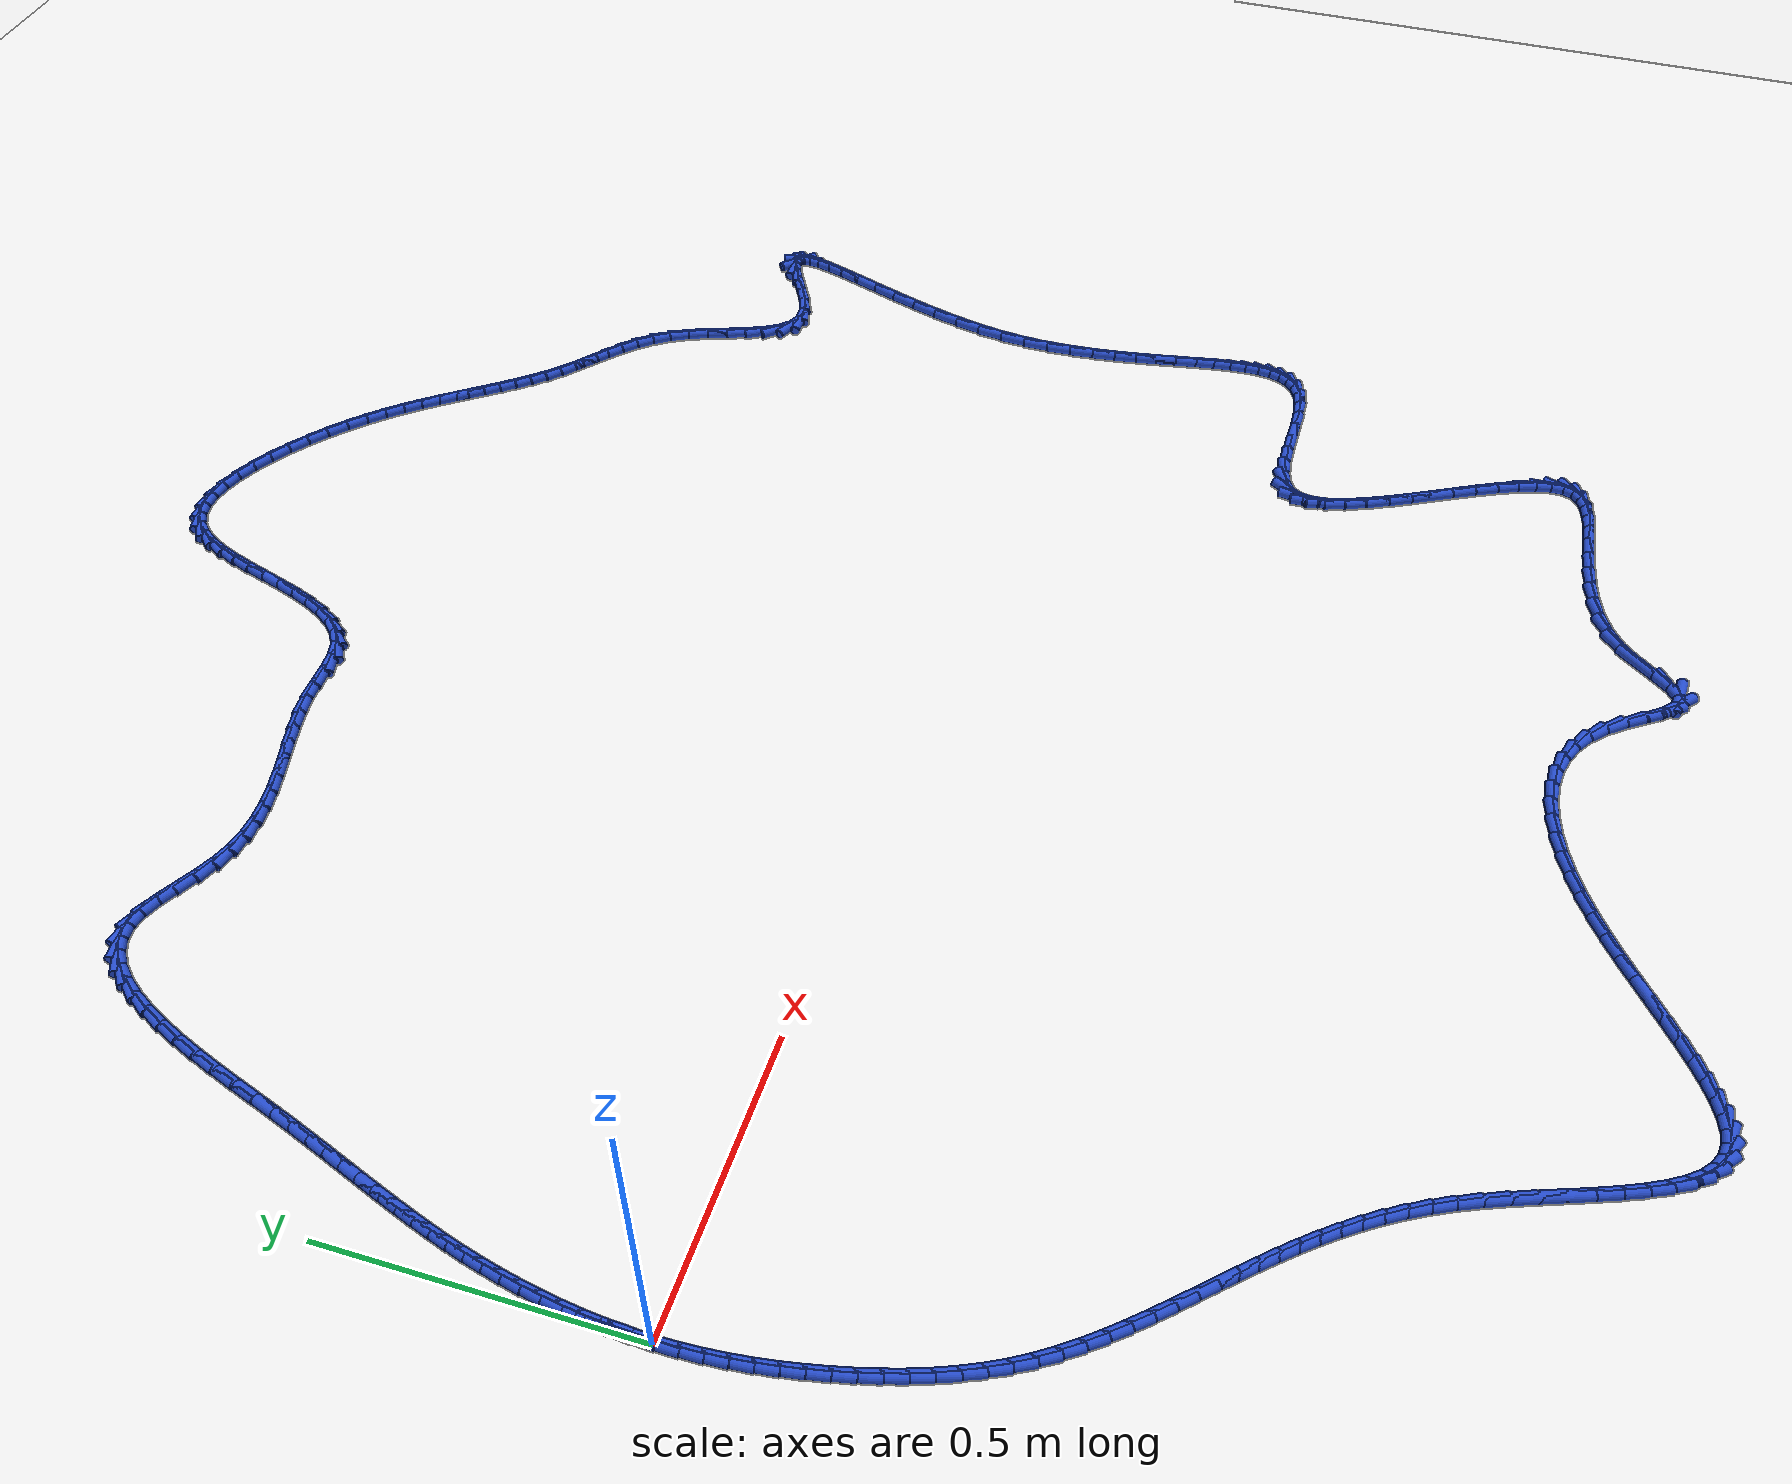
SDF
<sdf version="1.6">
 <world name="default">
  <light name="sun" type="directional">
   <pose>0 0 10 0 -0 0</pose>
   <diffuse>0.8 0.8 0.8 1</diffuse>
   <specular>0.2 0.2 0.2 1</specular>
   <attenuation>
    <range>1000</range>
    <constant>0.9</constant>
    <linear>0.01</linear>
    <quadratic>0.001</quadratic>
   </attenuation>
   <direction>-0.5 0.1 -0.9</direction>
  </light>
  <model name="ground_plane">
   <static>1</static>
   <link name="link">
    <collision name="collision">
     <geometry><plane><normal>0 0 1</normal><size>100 100</size></plane></geometry>
     <surface><friction><ode><mu>100</mu><mu2>50</mu2></ode></friction></surface>
    </collision>
    <visual name="visual">
     <cast_shadows>0</cast_shadows>
     <geometry><plane><normal>0 0 1</normal><size>100 100</size></plane></geometry>
     <material>
      <script><uri>file://media/materials/scripts/gazebo.material</uri><name>Gazebo/WhiteGlow</name></script>
     </material>
    </visual>
   </link>
  </model>
  <gravity>0 0 -9.8</gravity>
  <magnetic_field>6e-06 2.3e-05 -4.2e-05</magnetic_field>
  <atmosphere type="adiabatic"/>
  <physics name="default_physics" default="0" type="ode">
   <max_step_size>0.001</max_step_size>
   <real_time_factor>1</real_time_factor>
   <real_time_update_rate>1000</real_time_update_rate>
  </physics>
  <scene><ambient>0.4 0.4 0.4 1</ambient><background>0.7 0.7 0.7 1</background><shadows>1</shadows></scene>
  <spherical_coordinates>
   <surface_model>EARTH_WGS84</surface_model>
   <latitude_deg>0</latitude_deg>
   <longitude_deg>0</longitude_deg>
   <elevation>0</elevation>
   <heading_deg>0</heading_deg>
  </spherical_coordinates>
  <model name="line">
   <link name="link_0">
    <pose>-1.3877787807814457e-17 -6.938893903907228e-18 0.01 0 1.57 1.5485829074068658</pose>
    <collision name="collision">
     <geometry><cylinder><radius>0.01</radius><length>0.08</length></cylinder></geometry>
    </collision>
    <visual name="visual">
     <material>
      <script><name>Gazebo/Blue</name><uri>file://media/materials/scripts/gazebo.material</uri></script>
     </material>
     <geometry><cylinder><radius>0.01</radius><length>0.08</length></cylinder></geometry>
    </visual>
   </link>
   <link name="link_1">
    <pose>0.0007429017941402904 0.0334383277805476 0.01 0 1.57 1.5134630559075293</pose>
    <collision name="collision">
     <geometry><cylinder><radius>0.01</radius><length>0.08</length></cylinder></geometry>
    </collision>
    <visual name="visual">
     <material>
      <script><name>Gazebo/Blue</name><uri>file://media/materials/scripts/gazebo.material</uri></script>
     </material>
     <geometry><cylinder><radius>0.01</radius><length>0.08</length></cylinder></geometry>
    </visual>
   </link>
   <link name="link_2">
    <pose>0.0026647057397864308 0.06692146473099614 0.01 0 1.57 1.4807141770336067</pose>
    <collision name="collision">
     <geometry><cylinder><radius>0.01</radius><length>0.08</length></cylinder></geometry>
    </collision>
    <visual name="visual">
     <material>
      <script><name>Gazebo/Blue</name><uri>file://media/materials/scripts/gazebo.material</uri></script>
     </material>
     <geometry><cylinder><radius>0.01</radius><length>0.08</length></cylinder></geometry>
    </visual>
   </link>
   <link name="link_3">
    <pose>0.005680466674889642 0.10030875733728085 0.01 0 1.57 1.4499795882810984</pose>
    <collision name="collision">
     <geometry><cylinder><radius>0.01</radius><length>0.08</length></cylinder></geometry>
    </collision>
    <visual name="visual">
     <material>
      <script><name>Gazebo/Blue</name><uri>file://media/materials/scripts/gazebo.material</uri></script>
     </material>
     <geometry><cylinder><radius>0.01</radius><length>0.08</length></cylinder></geometry>
    </visual>
   </link>
   <link name="link_4">
    <pose>0.00970523943740116 0.13345955208533702 0.01 0 1.57 1.4209279527296843</pose>
    <collision name="collision">
     <geometry><cylinder><radius>0.01</radius><length>0.08</length></cylinder></geometry>
    </collision>
    <visual name="visual">
     <material>
      <script><name>Gazebo/Blue</name><uri>file://media/materials/scripts/gazebo.material</uri></script>
     </material>
     <geometry><cylinder><radius>0.01</radius><length>0.08</length></cylinder></geometry>
    </visual>
   </link>
   <link name="link_5">
    <pose>0.014654078865272233 0.16623319546109994 0.01 0 1.57 1.393246669650324</pose>
    <collision name="collision">
     <geometry><cylinder><radius>0.01</radius><length>0.08</length></cylinder></geometry>
    </collision>
    <visual name="visual">
     <material>
      <script><name>Gazebo/Blue</name><uri>file://media/materials/scripts/gazebo.material</uri></script>
     </material>
     <geometry><cylinder><radius>0.01</radius><length>0.08</length></cylinder></geometry>
    </visual>
   </link>
   <link name="link_6">
    <pose>0.020442039796454085 0.19848903395050485 0.01 0 1.57 1.366634245378856</pose>
    <collision name="collision">
     <geometry><cylinder><radius>0.01</radius><length>0.08</length></cylinder></geometry>
    </collision>
    <visual name="visual">
     <material>
      <script><name>Gazebo/Blue</name><uri>file://media/materials/scripts/gazebo.material</uri></script>
     </material>
     <geometry><cylinder><radius>0.01</radius><length>0.08</length></cylinder></geometry>
    </visual>
   </link>
   <link name="link_7">
    <pose>0.026984177068897962 0.230086414039487 0.01 0 1.57 1.3408448167251408</pose>
    <collision name="collision">
     <geometry><cylinder><radius>0.01</radius><length>0.08</length></cylinder></geometry>
    </collision>
    <visual name="visual">
     <material>
      <script><name>Gazebo/Blue</name><uri>file://media/materials/scripts/gazebo.material</uri></script>
     </material>
     <geometry><cylinder><radius>0.01</radius><length>0.08</length></cylinder></geometry>
    </visual>
   </link>
   <link name="link_8">
    <pose>0.03419856837596608 0.26090500114363857 0.01 0 1.57 1.3163476057362486</pose>
    <collision name="collision">
     <geometry><cylinder><radius>0.01</radius><length>0.08</length></cylinder></geometry>
    </collision>
    <visual name="visual">
     <material>
      <script><name>Gazebo/Blue</name><uri>file://media/materials/scripts/gazebo.material</uri></script>
     </material>
     <geometry><cylinder><radius>0.01</radius><length>0.08</length></cylinder></geometry>
    </visual>
   </link>
   <link name="link_9">
    <pose>0.042034146527451445 0.2910318615810336 0.01 0 1.57 1.293926488512192</pose>
    <collision name="collision">
     <geometry><cylinder><radius>0.01</radius><length>0.08</length></cylinder></geometry>
    </collision>
    <visual name="visual">
     <material>
      <script><name>Gazebo/Blue</name><uri>file://media/materials/scripts/gazebo.material</uri></script>
     </material>
     <geometry><cylinder><radius>0.01</radius><length>0.08</length></cylinder></geometry>
    </visual>
   </link>
   <link name="link_10">
    <pose>0.05045788841886612 0.32067534980913776 0.01 0 1.57 1.2740965692798139</pose>
    <collision name="collision">
     <geometry><cylinder><radius>0.01</radius><length>0.08</length></cylinder></geometry>
    </collision>
    <visual name="visual">
     <material>
      <script><name>Gazebo/Blue</name><uri>file://media/materials/scripts/gazebo.material</uri></script>
     </material>
     <geometry><cylinder><radius>0.01</radius><length>0.08</length></cylinder></geometry>
    </visual>
   </link>
   <link name="link_11">
    <pose>0.059436998082770635 0.3500453470477267 0.01 0 1.57 1.257271168092173</pose>
    <collision name="collision">
     <geometry><cylinder><radius>0.01</radius><length>0.08</length></cylinder></geometry>
    </collision>
    <visual name="visual">
     <material>
      <script><name>Gazebo/Blue</name><uri>file://media/materials/scripts/gazebo.material</uri></script>
     </material>
     <geometry><cylinder><radius>0.01</radius><length>0.08</length></cylinder></geometry>
    </visual>
   </link>
   <link name="link_12">
    <pose>0.06893867955172554 0.37935173451657617 0.01 0 1.57 1.2437411347839498</pose>
    <collision name="collision">
     <geometry><cylinder><radius>0.01</radius><length>0.08</length></cylinder></geometry>
    </collision>
    <visual name="visual">
     <material>
      <script><name>Gazebo/Blue</name><uri>file://media/materials/scripts/gazebo.material</uri></script>
     </material>
     <geometry><cylinder><radius>0.01</radius><length>0.08</length></cylinder></geometry>
    </visual>
   </link>
   <link name="link_13">
    <pose>0.07893013685829134 0.40880439343546165 0.01 0 1.57 1.2336627364881174</pose>
    <collision name="collision">
     <geometry><cylinder><radius>0.01</radius><length>0.08</length></cylinder></geometry>
    </collision>
    <visual name="visual">
     <material>
      <script><name>Gazebo/Blue</name><uri>file://media/materials/scripts/gazebo.material</uri></script>
     </material>
     <geometry><cylinder><radius>0.01</radius><length>0.08</length></cylinder></geometry>
    </visual>
   </link>
   <link name="link_14">
    <pose>0.08937857403502862 0.4386132050241591 0.01 0 1.57 1.2270583333097542</pose>
    <collision name="collision">
     <geometry><cylinder><radius>0.01</radius><length>0.08</length></cylinder></geometry>
    </collision>
    <visual name="visual">
     <material>
      <script><name>Gazebo/Blue</name><uri>file://media/materials/scripts/gazebo.material</uri></script>
     </material>
     <geometry><cylinder><radius>0.01</radius><length>0.08</length></cylinder></geometry>
    </visual>
   </link>
   <link name="link_15">
    <pose>0.10025119511449786 0.46898805050244396 0.01 0 1.57 1.2238280481717299</pose>
    <collision name="collision">
     <geometry><cylinder><radius>0.01</radius><length>0.08</length></cylinder></geometry>
    </collision>
    <visual name="visual">
     <material>
      <script><name>Gazebo/Blue</name><uri>file://media/materials/scripts/gazebo.material</uri></script>
     </material>
     <geometry><cylinder><radius>0.01</radius><length>0.08</length></cylinder></geometry>
    </visual>
   </link>
   <link name="link_16">
    <pose>0.11151520412925965 0.5001388110900922 0.01 0 1.57 1.2237693961591118</pose>
    <collision name="collision">
     <geometry><cylinder><radius>0.01</radius><length>0.08</length></cylinder></geometry>
    </collision>
    <visual name="visual">
     <material>
      <script><name>Gazebo/Blue</name><uri>file://media/materials/scripts/gazebo.material</uri></script>
     </material>
     <geometry><cylinder><radius>0.01</radius><length>0.08</length></cylinder></geometry>
    </visual>
   </link>
   <link name="link_17">
    <pose>0.12313780511187447 0.5322753680068792 0.01 0 1.57 1.2266014269598087</pose>
    <collision name="collision">
     <geometry><cylinder><radius>0.01</radius><length>0.08</length></cylinder></geometry>
    </collision>
    <visual name="visual">
     <material>
      <script><name>Gazebo/Blue</name><uri>file://media/materials/scripts/gazebo.material</uri></script>
     </material>
     <geometry><cylinder><radius>0.01</radius><length>0.08</length></cylinder></geometry>
    </visual>
   </link>
   <link name="link_18">
    <pose>0.1350862020949029 0.5656076024725809 0.01 0 1.57 1.2319901800391935</pose>
    <collision name="collision">
     <geometry><cylinder><radius>0.01</radius><length>0.08</length></cylinder></geometry>
    </collision>
    <visual name="visual">
     <material>
      <script><name>Gazebo/Blue</name><uri>file://media/materials/scripts/gazebo.material</uri></script>
     </material>
     <geometry><cylinder><radius>0.01</radius><length>0.08</length></cylinder></geometry>
    </visual>
   </link>
   <link name="link_19">
    <pose>0.14732759911090548 0.600345395706973 0.01 0 1.57 1.2395728927162282</pose>
    <collision name="collision">
     <geometry><cylinder><radius>0.01</radius><length>0.08</length></cylinder></geometry>
    </collision>
    <visual name="visual">
     <material>
      <script><name>Gazebo/Blue</name><uri>file://media/materials/scripts/gazebo.material</uri></script>
     </material>
     <geometry><cylinder><radius>0.01</radius><length>0.08</length></cylinder></geometry>
    </visual>
   </link>
   <link name="link_20">
    <pose>0.15982920019244273 0.6366986289298311 0.01 0 1.57 1.248035596796909</pose>
    <collision name="collision">
     <geometry><cylinder><radius>0.01</radius><length>0.08</length></cylinder></geometry>
    </collision>
    <visual name="visual">
     <material>
      <script><name>Gazebo/Blue</name><uri>file://media/materials/scripts/gazebo.material</uri></script>
     </material>
     <geometry><cylinder><radius>0.01</radius><length>0.08</length></cylinder></geometry>
    </visual>
   </link>
   <link name="link_21">
    <pose>0.17257158185329466 0.6747974423504048 0.01 0 1.57 1.2503602949276234</pose>
    <collision name="collision">
     <geometry><cylinder><radius>0.01</radius><length>0.08</length></cylinder></geometry>
    </collision>
    <visual name="visual">
     <material>
      <script><name>Gazebo/Blue</name><uri>file://media/materials/scripts/gazebo.material</uri></script>
     </material>
     <geometry><cylinder><radius>0.01</radius><length>0.08</length></cylinder></geometry>
    </visual>
   </link>
   <link name="link_22">
    <pose>0.18563694767771882 0.714165967078835 0.01 0 1.57 1.2440328463826626</pose>
    <collision name="collision">
     <geometry><cylinder><radius>0.01</radius><length>0.08</length></cylinder></geometry>
    </collision>
    <visual name="visual">
     <material>
      <script><name>Gazebo/Blue</name><uri>file://media/materials/scripts/gazebo.material</uri></script>
     </material>
     <geometry><cylinder><radius>0.01</radius><length>0.08</length></cylinder></geometry>
    </visual>
   </link>
   <link name="link_23">
    <pose>0.19915416839653147 0.7540500548720234 0.01 0 1.57 1.2291241233278682</pose>
    <collision name="collision">
     <geometry><cylinder><radius>0.01</radius><length>0.08</length></cylinder></geometry>
    </collision>
    <visual name="visual">
     <material>
      <script><name>Gazebo/Blue</name><uri>file://media/materials/scripts/gazebo.material</uri></script>
     </material>
     <geometry><cylinder><radius>0.01</radius><length>0.08</length></cylinder></geometry>
    </visual>
   </link>
   <link name="link_24">
    <pose>0.21325235990821334 0.7936940955354963 0.01 0 1.57 1.2048962785733868</pose>
    <collision name="collision">
     <geometry><cylinder><radius>0.01</radius><length>0.08</length></cylinder></geometry>
    </collision>
    <visual name="visual">
     <material>
      <script><name>Gazebo/Blue</name><uri>file://media/materials/scripts/gazebo.material</uri></script>
     </material>
     <geometry><cylinder><radius>0.01</radius><length>0.08</length></cylinder></geometry>
    </visual>
   </link>
   <link name="link_25">
    <pose>0.228060638111245 0.8323424788747815 0.01 0 1.57 1.169701695958854</pose>
    <collision name="collision">
     <geometry><cylinder><radius>0.01</radius><length>0.08</length></cylinder></geometry>
    </collision>
    <visual name="visual">
     <material>
      <script><name>Gazebo/Blue</name><uri>file://media/materials/scripts/gazebo.material</uri></script>
     </material>
     <geometry><cylinder><radius>0.01</radius><length>0.08</length></cylinder></geometry>
    </visual>
   </link>
   <link name="link_26">
    <pose>0.24370811890410699 0.8692395946954052 0.01 0 1.57 1.12071568485605</pose>
    <collision name="collision">
     <geometry><cylinder><radius>0.01</radius><length>0.08</length></cylinder></geometry>
    </collision>
    <visual name="visual">
     <material>
      <script><name>Gazebo/Blue</name><uri>file://media/materials/scripts/gazebo.material</uri></script>
     </material>
     <geometry><cylinder><radius>0.01</radius><length>0.08</length></cylinder></geometry>
    </visual>
   </link>
   <link name="link_27">
    <pose>0.26032391818528 0.9036298328028944 0.01 0 1.57 1.0534454320064823</pose>
    <collision name="collision">
     <geometry><cylinder><radius>0.01</radius><length>0.08</length></cylinder></geometry>
    </collision>
    <visual name="visual">
     <material>
      <script><name>Gazebo/Blue</name><uri>file://media/materials/scripts/gazebo.material</uri></script>
     </material>
     <geometry><cylinder><radius>0.01</radius><length>0.08</length></cylinder></geometry>
    </visual>
   </link>
   <link name="link_28">
    <pose>0.27803715185324474 0.9347575830027761 0.01 0 1.57 0.96098626019706</pose>
    <collision name="collision">
     <geometry><cylinder><radius>0.01</radius><length>0.08</length></cylinder></geometry>
    </collision>
    <visual name="visual">
     <material>
      <script><name>Gazebo/Blue</name><uri>file://media/materials/scripts/gazebo.material</uri></script>
     </material>
     <geometry><cylinder><radius>0.01</radius><length>0.08</length></cylinder></geometry>
    </visual>
   </link>
   <link name="link_29">
    <pose>0.2969769358064819 0.9618672351005776 0.01 0 1.57 0.8332253021852252</pose>
    <collision name="collision">
     <geometry><cylinder><radius>0.01</radius><length>0.08</length></cylinder></geometry>
    </collision>
    <visual name="visual">
     <material>
      <script><name>Gazebo/Blue</name><uri>file://media/materials/scripts/gazebo.material</uri></script>
     </material>
     <geometry><cylinder><radius>0.01</radius><length>0.08</length></cylinder></geometry>
    </visual>
   </link>
   <link name="link_30">
    <pose>0.3172723859434718 0.9842031789018248 0.01 0 1.57 0.6572111232838885</pose>
    <collision name="collision">
     <geometry><cylinder><radius>0.01</radius><length>0.08</length></cylinder></geometry>
    </collision>
    <visual name="visual">
     <material>
      <script><name>Gazebo/Blue</name><uri>file://media/materials/scripts/gazebo.material</uri></script>
     </material>
     <geometry><cylinder><radius>0.01</radius><length>0.08</length></cylinder></geometry>
    </visual>
   </link>
   <link name="link_31">
    <pose>0.33905261816269533 1.0010098042120454 0.01 0 1.57 0.4226526396820982</pose>
    <collision name="collision">
     <geometry><cylinder><radius>0.01</radius><length>0.08</length></cylinder></geometry>
    </collision>
    <visual name="visual">
     <material>
      <script><name>Gazebo/Blue</name><uri>file://media/materials/scripts/gazebo.material</uri></script>
     </material>
     <geometry><cylinder><radius>0.01</radius><length>0.08</length></cylinder></geometry>
    </visual>
   </link>
   <link name="link_32">
    <pose>0.36244674836263313 1.0115315008367658 0.01 0 1.57 0.13761133147089463</pose>
    <collision name="collision">
     <geometry><cylinder><radius>0.01</radius><length>0.08</length></cylinder></geometry>
    </collision>
    <visual name="visual">
     <material>
      <script><name>Gazebo/Blue</name><uri>file://media/materials/scripts/gazebo.material</uri></script>
     </material>
     <geometry><cylinder><radius>0.01</radius><length>0.08</length></cylinder></geometry>
    </visual>
   </link>
   <link name="link_33">
    <pose>0.3875838924417656 1.0150126585815133 0.01 0 1.57 -0.15613693400782325</pose>
    <collision name="collision">
     <geometry><cylinder><radius>0.01</radius><length>0.08</length></cylinder></geometry>
    </collision>
    <visual name="visual">
     <material>
      <script><name>Gazebo/Blue</name><uri>file://media/materials/scripts/gazebo.material</uri></script>
     </material>
     <geometry><cylinder><radius>0.01</radius><length>0.08</length></cylinder></geometry>
    </visual>
   </link>
   <link name="link_34">
    <pose>0.41458370208011375 1.0107623961370753 0.01 0 1.57 -0.36606578916136967</pose>
    <collision name="collision">
     <geometry><cylinder><radius>0.01</radius><length>0.08</length></cylinder></geometry>
    </collision>
    <visual name="visual">
     <material>
      <script><name>Gazebo/Blue</name><uri>file://media/materials/scripts/gazebo.material</uri></script>
     </material>
     <geometry><cylinder><radius>0.01</radius><length>0.08</length></cylinder></geometry>
    </visual>
   </link>
   <link name="link_35">
    <pose>0.443323814632774 0.9997450473116573 0.01 0 1.57 -0.46407062809870164</pose>
    <collision name="collision">
     <geometry><cylinder><radius>0.01</radius><length>0.08</length></cylinder></geometry>
    </collision>
    <visual name="visual">
     <material>
      <script><name>Gazebo/Blue</name><uri>file://media/materials/scripts/gazebo.material</uri></script>
     </material>
     <geometry><cylinder><radius>0.01</radius><length>0.08</length></cylinder></geometry>
    </visual>
   </link>
   <link name="link_36">
    <pose>0.47342550670559924 0.9846782809187054 0.01 0 1.57 -0.4834780515167525</pose>
    <collision name="collision">
     <geometry><cylinder><radius>0.01</radius><length>0.08</length></cylinder></geometry>
    </collision>
    <visual name="visual">
     <material>
      <script><name>Gazebo/Blue</name><uri>file://media/materials/scripts/gazebo.material</uri></script>
     </material>
     <geometry><cylinder><radius>0.01</radius><length>0.08</length></cylinder></geometry>
    </visual>
   </link>
   <link name="link_37">
    <pose>0.504497718417748 0.9683641390387474 0.01 0 1.57 -0.43633383077724097</pose>
    <collision name="collision">
     <geometry><cylinder><radius>0.01</radius><length>0.08</length></cylinder></geometry>
    </collision>
    <visual name="visual">
     <material>
      <script><name>Gazebo/Blue</name><uri>file://media/materials/scripts/gazebo.material</uri></script>
     </material>
     <geometry><cylinder><radius>0.01</radius><length>0.08</length></cylinder></geometry>
    </visual>
   </link>
   <link name="link_38">
    <pose>0.5361493898883783 0.9536046637523096 0.01 0 1.57 -0.3187283572391451</pose>
    <collision name="collision">
     <geometry><cylinder><radius>0.01</radius><length>0.08</length></cylinder></geometry>
    </collision>
    <visual name="visual">
     <material>
      <script><name>Gazebo/Blue</name><uri>file://media/materials/scripts/gazebo.material</uri></script>
     </material>
     <geometry><cylinder><radius>0.01</radius><length>0.08</length></cylinder></geometry>
    </visual>
   </link>
   <link name="link_39">
    <pose>0.5680024422446137 0.9430938347623454 0.01 0 1.57 -0.16856508030482098</pose>
    <collision name="collision">
     <geometry><cylinder><radius>0.01</radius><length>0.08</length></cylinder></geometry>
    </collision>
    <visual name="visual">
     <material>
      <script><name>Gazebo/Blue</name><uri>file://media/materials/scripts/gazebo.material</uri></script>
     </material>
     <geometry><cylinder><radius>0.01</radius><length>0.08</length></cylinder></geometry>
    </visual>
   </link>
   <link name="link_40">
    <pose>0.5999022909631823 0.9376651190244988 0.01 0 1.57 -0.03379384773260507</pose>
    <collision name="collision">
     <geometry><cylinder><radius>0.01</radius><length>0.08</length></cylinder></geometry>
    </collision>
    <visual name="visual">
     <material>
      <script><name>Gazebo/Blue</name><uri>file://media/materials/scripts/gazebo.material</uri></script>
     </material>
     <geometry><cylinder><radius>0.01</radius><length>0.08</length></cylinder></geometry>
    </visual>
   </link>
   <link name="link_41">
    <pose>0.6318827098355708 0.9365839660197505 0.01 0 1.57 0.07719156503482295</pose>
    <collision name="collision">
     <geometry><cylinder><radius>0.01</radius><length>0.08</length></cylinder></geometry>
    </collision>
    <visual name="visual">
     <material>
      <script><name>Gazebo/Blue</name><uri>file://media/materials/scripts/gazebo.material</uri></script>
     </material>
     <geometry><cylinder><radius>0.01</radius><length>0.08</length></cylinder></geometry>
    </visual>
   </link>
   <link name="link_42">
    <pose>0.6639833619470645 0.9390667989060257 0.01 0 1.57 0.16172310763942283</pose>
    <collision name="collision">
     <geometry><cylinder><radius>0.01</radius><length>0.08</length></cylinder></geometry>
    </collision>
    <visual name="visual">
     <material>
      <script><name>Gazebo/Blue</name><uri>file://media/materials/scripts/gazebo.material</uri></script>
     </material>
     <geometry><cylinder><radius>0.01</radius><length>0.08</length></cylinder></geometry>
    </visual>
   </link>
   <link name="link_43">
    <pose>0.6962439103829482 0.9443300408412509 0.01 0 1.57 0.2200400076044063</pose>
    <collision name="collision">
     <geometry><cylinder><radius>0.01</radius><length>0.08</length></cylinder></geometry>
    </collision>
    <visual name="visual">
     <material>
      <script><name>Gazebo/Blue</name><uri>file://media/materials/scripts/gazebo.material</uri></script>
     </material>
     <geometry><cylinder><radius>0.01</radius><length>0.08</length></cylinder></geometry>
    </visual>
   </link>
   <link name="link_44">
    <pose>0.7287040182285066 0.9515901149833521 0.01 0 1.57 0.25355159955457574</pose>
    <collision name="collision">
     <geometry><cylinder><radius>0.01</radius><length>0.08</length></cylinder></geometry>
    </collision>
    <visual name="visual">
     <material>
      <script><name>Gazebo/Blue</name><uri>file://media/materials/scripts/gazebo.material</uri></script>
     </material>
     <geometry><cylinder><radius>0.01</radius><length>0.08</length></cylinder></geometry>
    </visual>
   </link>
   <link name="link_45">
    <pose>0.7614033485690254 0.9600634444902549 0.01 0 1.57 0.2636804550011287</pose>
    <collision name="collision">
     <geometry><cylinder><radius>0.01</radius><length>0.08</length></cylinder></geometry>
    </collision>
    <visual name="visual">
     <material>
      <script><name>Gazebo/Blue</name><uri>file://media/materials/scripts/gazebo.material</uri></script>
     </material>
     <geometry><cylinder><radius>0.01</radius><length>0.08</length></cylinder></geometry>
    </visual>
   </link>
   <link name="link_46">
    <pose>0.7943815644897892 0.9689664525198854 0.01 0 1.57 0.2513261055935245</pose>
    <collision name="collision">
     <geometry><cylinder><radius>0.01</radius><length>0.08</length></cylinder></geometry>
    </collision>
    <visual name="visual">
     <material>
      <script><name>Gazebo/Blue</name><uri>file://media/materials/scripts/gazebo.material</uri></script>
     </material>
     <geometry><cylinder><radius>0.01</radius><length>0.08</length></cylinder></geometry>
    </visual>
   </link>
   <link name="link_47">
    <pose>0.8276783290760833 0.9775155622301696 0.01 0 1.57 0.21676398331153515</pose>
    <collision name="collision">
     <geometry><cylinder><radius>0.01</radius><length>0.08</length></cylinder></geometry>
    </collision>
    <visual name="visual">
     <material>
      <script><name>Gazebo/Blue</name><uri>file://media/materials/scripts/gazebo.material</uri></script>
     </material>
     <geometry><cylinder><radius>0.01</radius><length>0.08</length></cylinder></geometry>
    </visual>
   </link>
   <link name="link_48">
    <pose>0.861333305413192 0.9849271967790327 0.01 0 1.57 0.1598612374495937</pose>
    <collision name="collision">
     <geometry><cylinder><radius>0.01</radius><length>0.08</length></cylinder></geometry>
    </collision>
    <visual name="visual">
     <material>
      <script><name>Gazebo/Blue</name><uri>file://media/materials/scripts/gazebo.material</uri></script>
     </material>
     <geometry><cylinder><radius>0.01</radius><length>0.08</length></cylinder></geometry>
    </visual>
   </link>
   <link name="link_49">
    <pose>0.8953861565864007 0.9904177793244016 0.01 0 1.57 0.08105850451711168</pose>
    <collision name="collision">
     <geometry><cylinder><radius>0.01</radius><length>0.08</length></cylinder></geometry>
    </collision>
    <visual name="visual">
     <material>
      <script><name>Gazebo/Blue</name><uri>file://media/materials/scripts/gazebo.material</uri></script>
     </material>
     <geometry><cylinder><radius>0.01</radius><length>0.08</length></cylinder></geometry>
    </visual>
   </link>
   <link name="link_50">
    <pose>0.9298706562489153 0.9932191795009903 0.01 0 1.57 0.026573679340926786</pose>
    <collision name="collision">
     <geometry><cylinder><radius>0.01</radius><length>0.08</length></cylinder></geometry>
    </collision>
    <visual name="visual">
     <material>
      <script><name>Gazebo/Blue</name><uri>file://media/materials/scripts/gazebo.material</uri></script>
     </material>
     <geometry><cylinder><radius>0.01</radius><length>0.08</length></cylinder></geometry>
    </visual>
   </link>
   <link name="link_51">
    <pose>0.9642223579543312 0.9941322455407474 0.01 0 1.57 0.08347506815033466</pose>
    <collision name="collision">
     <geometry><cylinder><radius>0.01</radius><length>0.08</length></cylinder></geometry>
    </collision>
    <visual name="visual">
     <material>
      <script><name>Gazebo/Blue</name><uri>file://media/materials/scripts/gazebo.material</uri></script>
     </material>
     <geometry><cylinder><radius>0.01</radius><length>0.08</length></cylinder></geometry>
    </visual>
   </link>
   <link name="link_52">
    <pose>0.9967719321276656 0.9968556520480873 0.01 0 1.57 0.2835726074988414</pose>
    <collision name="collision">
     <geometry><cylinder><radius>0.01</radius><length>0.08</length></cylinder></geometry>
    </collision>
    <visual name="visual">
     <material>
      <script><name>Gazebo/Blue</name><uri>file://media/materials/scripts/gazebo.material</uri></script>
     </material>
     <geometry><cylinder><radius>0.01</radius><length>0.08</length></cylinder></geometry>
    </visual>
   </link>
   <link name="link_53">
    <pose>1.0257741973815702 1.005307675988852 0.01 0 1.57 0.5647721013559556</pose>
    <collision name="collision">
     <geometry><cylinder><radius>0.01</radius><length>0.08</length></cylinder></geometry>
    </collision>
    <visual name="visual">
     <material>
      <script><name>Gazebo/Blue</name><uri>file://media/materials/scripts/gazebo.material</uri></script>
     </material>
     <geometry><cylinder><radius>0.01</radius><length>0.08</length></cylinder></geometry>
    </visual>
   </link>
   <link name="link_54">
    <pose>1.0505899475597635 1.021031366743377 0.01 0 1.57 0.8055773772842348</pose>
    <collision name="collision">
     <geometry><cylinder><radius>0.01</radius><length>0.08</length></cylinder></geometry>
    </collision>
    <visual name="visual">
     <material>
      <script><name>Gazebo/Blue</name><uri>file://media/materials/scripts/gazebo.material</uri></script>
     </material>
     <geometry><cylinder><radius>0.01</radius><length>0.08</length></cylinder></geometry>
    </visual>
   </link>
   <link name="link_55">
    <pose>1.0717480807830457 1.0430611157910508 0.01 0 1.57 0.9848641976815936</pose>
    <collision name="collision">
     <geometry><cylinder><radius>0.01</radius><length>0.08</length></cylinder></geometry>
    </collision>
    <visual name="visual">
     <material>
      <script><name>Gazebo/Blue</name><uri>file://media/materials/scripts/gazebo.material</uri></script>
     </material>
     <geometry><cylinder><radius>0.01</radius><length>0.08</length></cylinder></geometry>
    </visual>
   </link>
   <link name="link_56">
    <pose>1.0898334221185275 1.0703112041224174 0.01 0 1.57 1.1095726935597143</pose>
    <collision name="collision">
     <geometry><cylinder><radius>0.01</radius><length>0.08</length></cylinder></geometry>
    </collision>
    <visual name="visual">
     <material>
      <script><name>Gazebo/Blue</name><uri>file://media/materials/scripts/gazebo.material</uri></script>
     </material>
     <geometry><cylinder><radius>0.01</radius><length>0.08</length></cylinder></geometry>
    </visual>
   </link>
   <link name="link_57">
    <pose>1.1054307966333201 1.1016959127280221 0.01 0 1.57 1.1922746276317209</pose>
    <collision name="collision">
     <geometry><cylinder><radius>0.01</radius><length>0.08</length></cylinder></geometry>
    </collision>
    <visual name="visual">
     <material>
      <script><name>Gazebo/Blue</name><uri>file://media/materials/scripts/gazebo.material</uri></script>
     </material>
     <geometry><cylinder><radius>0.01</radius><length>0.08</length></cylinder></geometry>
    </visual>
   </link>
   <link name="link_58">
    <pose>1.1191250293945343 1.136129522598409 0.01 0 1.57 1.2430330259783198</pose>
    <collision name="collision">
     <geometry><cylinder><radius>0.01</radius><length>0.08</length></cylinder></geometry>
    </collision>
    <visual name="visual">
     <material>
      <script><name>Gazebo/Blue</name><uri>file://media/materials/scripts/gazebo.material</uri></script>
     </material>
     <geometry><cylinder><radius>0.01</radius><length>0.08</length></cylinder></geometry>
    </visual>
   </link>
   <link name="link_59">
    <pose>1.1315009454692815 1.1725263147241234 0.01 0 1.57 1.2680527440014207</pose>
    <collision name="collision">
     <geometry><cylinder><radius>0.01</radius><length>0.08</length></cylinder></geometry>
    </collision>
    <visual name="visual">
     <material>
      <script><name>Gazebo/Blue</name><uri>file://media/materials/scripts/gazebo.material</uri></script>
     </material>
     <geometry><cylinder><radius>0.01</radius><length>0.08</length></cylinder></geometry>
    </visual>
   </link>
   <link name="link_60">
    <pose>1.1431433699246718 1.2098005700957086 0.01 0 1.57 1.2701094827285944</pose>
    <collision name="collision">
     <geometry><cylinder><radius>0.01</radius><length>0.08</length></cylinder></geometry>
    </collision>
    <visual name="visual">
     <material>
      <script><name>Gazebo/Blue</name><uri>file://media/materials/scripts/gazebo.material</uri></script>
     </material>
     <geometry><cylinder><radius>0.01</radius><length>0.08</length></cylinder></geometry>
    </visual>
   </link>
   <link name="link_61">
    <pose>1.1546371278278174 1.2468665697037105 0.01 0 1.57 1.2488971349572502</pose>
    <collision name="collision">
     <geometry><cylinder><radius>0.01</radius><length>0.08</length></cylinder></geometry>
    </collision>
    <visual name="visual">
     <material>
      <script><name>Gazebo/Blue</name><uri>file://media/materials/scripts/gazebo.material</uri></script>
     </material>
     <geometry><cylinder><radius>0.01</radius><length>0.08</length></cylinder></geometry>
    </visual>
   </link>
   <link name="link_62">
    <pose>1.166567044245829 1.2826385945386738 0.01 0 1.57 1.2008159828431813</pose>
    <collision name="collision">
     <geometry><cylinder><radius>0.01</radius><length>0.08</length></cylinder></geometry>
    </collision>
    <visual name="visual">
     <material>
      <script><name>Gazebo/Blue</name><uri>file://media/materials/scripts/gazebo.material</uri></script>
     </material>
     <geometry><cylinder><radius>0.01</radius><length>0.08</length></cylinder></geometry>
    </visual>
   </link>
   <link name="link_63">
    <pose>1.1795179442458164 1.316030925591142 0.01 0 1.57 1.118080885438635</pose>
    <collision name="collision">
     <geometry><cylinder><radius>0.01</radius><length>0.08</length></cylinder></geometry>
    </collision>
    <visual name="visual">
     <material>
      <script><name>Gazebo/Blue</name><uri>file://media/materials/scripts/gazebo.material</uri></script>
     </material>
     <geometry><cylinder><radius>0.01</radius><length>0.08</length></cylinder></geometry>
    </visual>
   </link>
   <link name="link_64">
    <pose>1.194074652894892 1.3459578438516606 0.01 0 1.57 0.9874418955823683</pose>
    <collision name="collision">
     <geometry><cylinder><radius>0.01</radius><length>0.08</length></cylinder></geometry>
    </collision>
    <visual name="visual">
     <material>
      <script><name>Gazebo/Blue</name><uri>file://media/materials/scripts/gazebo.material</uri></script>
     </material>
     <geometry><cylinder><radius>0.01</radius><length>0.08</length></cylinder></geometry>
    </visual>
   </link>
   <link name="link_65">
    <pose>1.2108219952601667 1.3713336303107742 0.01 0 1.57 0.7909030731148624</pose>
    <collision name="collision">
     <geometry><cylinder><radius>0.01</radius><length>0.08</length></cylinder></geometry>
    </collision>
    <visual name="visual">
     <material>
      <script><name>Gazebo/Blue</name><uri>file://media/materials/scripts/gazebo.material</uri></script>
     </material>
     <geometry><cylinder><radius>0.01</radius><length>0.08</length></cylinder></geometry>
    </visual>
   </link>
   <link name="link_66">
    <pose>1.2303447964087508 1.391072565959027 0.01 0 1.57 0.5227936763117119</pose>
    <collision name="collision">
     <geometry><cylinder><radius>0.01</radius><length>0.08</length></cylinder></geometry>
    </collision>
    <visual name="visual">
     <material>
      <script><name>Gazebo/Blue</name><uri>file://media/materials/scripts/gazebo.material</uri></script>
     </material>
     <geometry><cylinder><radius>0.01</radius><length>0.08</length></cylinder></geometry>
    </visual>
   </link>
   <link name="link_67">
    <pose>1.2531465178950798 1.4042126804977495 0.01 0 1.57 0.2498852638311327</pose>
    <collision name="collision">
     <geometry><cylinder><radius>0.01</radius><length>0.08</length></cylinder></geometry>
    </collision>
    <visual name="visual">
     <material>
      <script><name>Gazebo/Blue</name><uri>file://media/materials/scripts/gazebo.material</uri></script>
     </material>
     <geometry><cylinder><radius>0.01</radius><length>0.08</length></cylinder></geometry>
    </visual>
   </link>
   <link name="link_68">
    <pose>1.2790519286141668 1.410824251854288 0.01 0 1.57 0.023380512775224793</pose>
    <collision name="collision">
     <geometry><cylinder><radius>0.01</radius><length>0.08</length></cylinder></geometry>
    </collision>
    <visual name="visual">
     <material>
      <script><name>Gazebo/Blue</name><uri>file://media/materials/scripts/gazebo.material</uri></script>
     </material>
     <geometry><cylinder><radius>0.01</radius><length>0.08</length></cylinder></geometry>
    </visual>
   </link>
   <link name="link_69">
    <pose>1.3075484534644417 1.4114906366480802 0.01 0 1.57 -0.15227370742326052</pose>
    <collision name="collision">
     <geometry><cylinder><radius>0.01</radius><length>0.08</length></cylinder></geometry>
    </collision>
    <visual name="visual">
     <material>
      <script><name>Gazebo/Blue</name><uri>file://media/materials/scripts/gazebo.material</uri></script>
     </material>
     <geometry><cylinder><radius>0.01</radius><length>0.08</length></cylinder></geometry>
    </visual>
   </link>
   <link name="link_70">
    <pose>1.3381210712657858 1.406798911827955 0.01 0 1.57 -0.2863857306144444</pose>
    <collision name="collision">
     <geometry><cylinder><radius>0.01</radius><length>0.08</length></cylinder></geometry>
    </collision>
    <visual name="visual">
     <material>
      <script><name>Gazebo/Blue</name><uri>file://media/materials/scripts/gazebo.material</uri></script>
     </material>
     <geometry><cylinder><radius>0.01</radius><length>0.08</length></cylinder></geometry>
    </visual>
   </link>
   <link name="link_71">
    <pose>1.3702547608380768 1.3973361543427387 0.01 0 1.57 -0.3902067045855018</pose>
    <collision name="collision">
     <geometry><cylinder><radius>0.01</radius><length>0.08</length></cylinder></geometry>
    </collision>
    <visual name="visual">
     <material>
      <script><name>Gazebo/Blue</name><uri>file://media/materials/scripts/gazebo.material</uri></script>
     </material>
     <geometry><cylinder><radius>0.01</radius><length>0.08</length></cylinder></geometry>
    </visual>
   </link>
   <link name="link_72">
    <pose>1.403434501001194 1.3836894411412592 0.01 0 1.57 -0.47281776665944075</pose>
    <collision name="collision">
     <geometry><cylinder><radius>0.01</radius><length>0.08</length></cylinder></geometry>
    </collision>
    <visual name="visual">
     <material>
      <script><name>Gazebo/Blue</name><uri>file://media/materials/scripts/gazebo.material</uri></script>
     </material>
     <geometry><cylinder><radius>0.01</radius><length>0.08</length></cylinder></geometry>
    </visual>
   </link>
   <link name="link_73">
    <pose>1.4371452705750165 1.366445849172344 0.01 0 1.57 -0.5407971714114908</pose>
    <collision name="collision">
     <geometry><cylinder><radius>0.01</radius><length>0.08</length></cylinder></geometry>
    </collision>
    <visual name="visual">
     <material>
      <script><name>Gazebo/Blue</name><uri>file://media/materials/scripts/gazebo.material</uri></script>
     </material>
     <geometry><cylinder><radius>0.01</radius><length>0.08</length></cylinder></geometry>
    </visual>
   </link>
   <link name="link_74">
    <pose>1.4708720483794233 1.3461924553848201 0.01 0 1.57 -0.5988465987437451</pose>
    <collision name="collision">
     <geometry><cylinder><radius>0.01</radius><length>0.08</length></cylinder></geometry>
    </collision>
    <visual name="visual">
     <material>
      <script><name>Gazebo/Blue</name><uri>file://media/materials/scripts/gazebo.material</uri></script>
     </material>
     <geometry><cylinder><radius>0.01</radius><length>0.08</length></cylinder></geometry>
    </visual>
   </link>
   <link name="link_75">
    <pose>1.5040998132342944 1.323516336727515 0.01 0 1.57 -0.6504473510956259</pose>
    <collision name="collision">
     <geometry><cylinder><radius>0.01</radius><length>0.08</length></cylinder></geometry>
    </collision>
    <visual name="visual">
     <material>
      <script><name>Gazebo/Blue</name><uri>file://media/materials/scripts/gazebo.material</uri></script>
     </material>
     <geometry><cylinder><radius>0.01</radius><length>0.08</length></cylinder></geometry>
    </visual>
   </link>
   <link name="link_76">
    <pose>1.536313543959507 1.2990045701492556 0.01 0 1.57 -0.6983771632394717</pose>
    <collision name="collision">
     <geometry><cylinder><radius>0.01</radius><length>0.08</length></cylinder></geometry>
    </collision>
    <visual name="visual">
     <material>
      <script><name>Gazebo/Blue</name><uri>file://media/materials/scripts/gazebo.material</uri></script>
     </material>
     <geometry><cylinder><radius>0.01</radius><length>0.08</length></cylinder></geometry>
    </visual>
   </link>
   <link name="link_77">
    <pose>1.5669982193749417 1.2732442325988702 0.01 0 1.57 -0.7451015140453114</pose>
    <collision name="collision">
     <geometry><cylinder><radius>0.01</radius><length>0.08</length></cylinder></geometry>
    </collision>
    <visual name="visual">
     <material>
      <script><name>Gazebo/Blue</name><uri>file://media/materials/scripts/gazebo.material</uri></script>
     </material>
     <geometry><cylinder><radius>0.01</radius><length>0.08</length></cylinder></geometry>
    </visual>
   </link>
   <link name="link_78">
    <pose>1.5956422322331263 1.2468204685296715 0.01 0 1.57 -0.7907930289481323</pose>
    <collision name="collision">
     <geometry><cylinder><radius>0.01</radius><length>0.08</length></cylinder></geometry>
    </collision>
    <visual name="visual">
     <material>
      <script><name>Gazebo/Blue</name><uri>file://media/materials/scripts/gazebo.material</uri></script>
     </material>
     <geometry><cylinder><radius>0.01</radius><length>0.08</length></cylinder></geometry>
    </visual>
   </link>
   <link name="link_79">
    <pose>1.6220200682367079 1.2201564762176067 0.01 0 1.57 -0.8318750491835111</pose>
    <collision name="collision">
     <geometry><cylinder><radius>0.01</radius><length>0.08</length></cylinder></geometry>
    </collision>
    <visual name="visual">
     <material>
      <script><name>Gazebo/Blue</name><uri>file://media/materials/scripts/gazebo.material</uri></script>
     </material>
     <geometry><cylinder><radius>0.01</radius><length>0.08</length></cylinder></geometry>
    </visual>
   </link>
   <link name="link_80">
    <pose>1.6464040287134705 1.1933936597263117 0.01 0 1.57 -0.8668220255298266</pose>
    <collision name="collision">
     <geometry><cylinder><radius>0.01</radius><length>0.08</length></cylinder></geometry>
    </collision>
    <visual name="visual">
     <material>
      <script><name>Gazebo/Blue</name><uri>file://media/materials/scripts/gazebo.material</uri></script>
     </material>
     <geometry><cylinder><radius>0.01</radius><length>0.08</length></cylinder></geometry>
    </visual>
   </link>
   <link name="link_81">
    <pose>1.6691162903649073 1.1666451905952933 0.01 0 1.57 -0.894545945794065</pose>
    <collision name="collision">
     <geometry><cylinder><radius>0.01</radius><length>0.08</length></cylinder></geometry>
    </collision>
    <visual name="visual">
     <material>
      <script><name>Gazebo/Blue</name><uri>file://media/materials/scripts/gazebo.material</uri></script>
     </material>
     <geometry><cylinder><radius>0.01</radius><length>0.08</length></cylinder></geometry>
    </visual>
   </link>
   <link name="link_82">
    <pose>1.6904790298925152 1.1400242403640606 0.01 0 1.57 -0.9140801477576073</pose>
    <collision name="collision">
     <geometry><cylinder><radius>0.01</radius><length>0.08</length></cylinder></geometry>
    </collision>
    <visual name="visual">
     <material>
      <script><name>Gazebo/Blue</name><uri>file://media/materials/scripts/gazebo.material</uri></script>
     </material>
     <geometry><cylinder><radius>0.01</radius><length>0.08</length></cylinder></geometry>
    </visual>
   </link>
   <link name="link_83">
    <pose>1.710814423997786 1.1136439805721197 0.01 0 1.57 -0.9245852969458827</pose>
    <collision name="collision">
     <geometry><cylinder><radius>0.01</radius><length>0.08</length></cylinder></geometry>
    </collision>
    <visual name="visual">
     <material>
      <script><name>Gazebo/Blue</name><uri>file://media/materials/scripts/gazebo.material</uri></script>
     </material>
     <geometry><cylinder><radius>0.01</radius><length>0.08</length></cylinder></geometry>
    </visual>
   </link>
   <link name="link_84">
    <pose>1.7304446493822163 1.08761758275898 0.01 0 1.57 -0.9253522137380359</pose>
    <collision name="collision">
     <geometry><cylinder><radius>0.01</radius><length>0.08</length></cylinder></geometry>
    </collision>
    <visual name="visual">
     <material>
      <script><name>Gazebo/Blue</name><uri>file://media/materials/scripts/gazebo.material</uri></script>
     </material>
     <geometry><cylinder><radius>0.01</radius><length>0.08</length></cylinder></geometry>
    </visual>
   </link>
   <link name="link_85">
    <pose>1.749691882747299 1.0620582184641487 0.01 0 1.57 -0.9158133650983236</pose>
    <collision name="collision">
     <geometry><cylinder><radius>0.01</radius><length>0.08</length></cylinder></geometry>
    </collision>
    <visual name="visual">
     <material>
      <script><name>Gazebo/Blue</name><uri>file://media/materials/scripts/gazebo.material</uri></script>
     </material>
     <geometry><cylinder><radius>0.01</radius><length>0.08</length></cylinder></geometry>
    </visual>
   </link>
   <link name="link_86">
    <pose>1.7688783007945292 1.0370790592271328 0.01 0 1.57 -0.8955746769448363</pose>
    <collision name="collision">
     <geometry><cylinder><radius>0.01</radius><length>0.08</length></cylinder></geometry>
    </collision>
    <visual name="visual">
     <material>
      <script><name>Gazebo/Blue</name><uri>file://media/materials/scripts/gazebo.material</uri></script>
     </material>
     <geometry><cylinder><radius>0.01</radius><length>0.08</length></cylinder></geometry>
    </visual>
   </link>
   <link name="link_87">
    <pose>1.7883260802254013 1.0127932765874412 0.01 0 1.57 -0.8644761535255147</pose>
    <collision name="collision">
     <geometry><cylinder><radius>0.01</radius><length>0.08</length></cylinder></geometry>
    </collision>
    <visual name="visual">
     <material>
      <script><name>Gazebo/Blue</name><uri>file://media/materials/scripts/gazebo.material</uri></script>
     </material>
     <geometry><cylinder><radius>0.01</radius><length>0.08</length></cylinder></geometry>
    </visual>
   </link>
   <link name="link_88">
    <pose>1.8083573977414094 0.9893140420845814 0.01 0 1.57 -0.822682287166682</pose>
    <collision name="collision">
     <geometry><cylinder><radius>0.01</radius><length>0.08</length></cylinder></geometry>
    </collision>
    <visual name="visual">
     <material>
      <script><name>Gazebo/Blue</name><uri>file://media/materials/scripts/gazebo.material</uri></script>
     </material>
     <geometry><cylinder><radius>0.01</radius><length>0.08</length></cylinder></geometry>
    </visual>
   </link>
   <link name="link_89">
    <pose>1.8292944300440483 0.9667545272580608 0.01 0 1.57 -0.7707899654025782</pose>
    <collision name="collision">
     <geometry><cylinder><radius>0.01</radius><length>0.08</length></cylinder></geometry>
    </collision>
    <visual name="visual">
     <material>
      <script><name>Gazebo/Blue</name><uri>file://media/materials/scripts/gazebo.material</uri></script>
     </material>
     <geometry><cylinder><radius>0.01</radius><length>0.08</length></cylinder></geometry>
    </visual>
   </link>
   <link name="link_90">
    <pose>1.8514593538348125 0.9452279036473872 0.01 0 1.57 -0.713066124969618</pose>
    <collision name="collision">
     <geometry><cylinder><radius>0.01</radius><length>0.08</length></cylinder></geometry>
    </collision>
    <visual name="visual">
     <material>
      <script><name>Gazebo/Blue</name><uri>file://media/materials/scripts/gazebo.material</uri></script>
     </material>
     <geometry><cylinder><radius>0.01</radius><length>0.08</length></cylinder></geometry>
    </visual>
   </link>
   <link name="link_91">
    <pose>1.8751015659429686 0.9247803663625813 0.01 0 1.57 -0.6765788130207413</pose>
    <collision name="collision">
     <geometry><cylinder><radius>0.01</radius><length>0.08</length></cylinder></geometry>
    </collision>
    <visual name="visual">
     <material>
      <script><name>Gazebo/Blue</name><uri>file://media/materials/scripts/gazebo.material</uri></script>
     </material>
     <geometry><cylinder><radius>0.01</radius><length>0.08</length></cylinder></geometry>
    </visual>
   </link>
   <link name="link_92">
    <pose>1.899861485021578 0.9048976920541428 0.01 0 1.57 -0.6732800599838428</pose>
    <collision name="collision">
     <geometry><cylinder><radius>0.01</radius><length>0.08</length></cylinder></geometry>
    </collision>
    <visual name="visual">
     <material>
      <script><name>Gazebo/Blue</name><uri>file://media/materials/scripts/gazebo.material</uri></script>
     </material>
     <geometry><cylinder><radius>0.01</radius><length>0.08</length></cylinder></geometry>
    </visual>
   </link>
   <link name="link_93">
    <pose>1.9250760516361756 0.8847863785265391 0.01 0 1.57 -0.7017515779665069</pose>
    <collision name="collision">
     <geometry><cylinder><radius>0.01</radius><length>0.08</length></cylinder></geometry>
    </collision>
    <visual name="visual">
     <material>
      <script><name>Gazebo/Blue</name><uri>file://media/materials/scripts/gazebo.material</uri></script>
     </material>
     <geometry><cylinder><radius>0.01</radius><length>0.08</length></cylinder></geometry>
    </visual>
   </link>
   <link name="link_94">
    <pose>1.9500799840331027 0.863650878472034 0.01 0 1.57 -0.760494613398068</pose>
    <collision name="collision">
     <geometry><cylinder><radius>0.01</radius><length>0.08</length></cylinder></geometry>
    </collision>
    <visual name="visual">
     <material>
      <script><name>Gazebo/Blue</name><uri>file://media/materials/scripts/gazebo.material</uri></script>
     </material>
     <geometry><cylinder><radius>0.01</radius><length>0.08</length></cylinder></geometry>
    </visual>
   </link>
   <link name="link_95">
    <pose>1.9742080004586995 0.8406956445828923 0.01 0 1.57 -0.8472763246064314</pose>
    <collision name="collision">
     <geometry><cylinder><radius>0.01</radius><length>0.08</length></cylinder></geometry>
    </collision>
    <visual name="visual">
     <material>
      <script><name>Gazebo/Blue</name><uri>file://media/materials/scripts/gazebo.material</uri></script>
     </material>
     <geometry><cylinder><radius>0.01</radius><length>0.08</length></cylinder></geometry>
    </visual>
   </link>
   <link name="link_96">
    <pose>1.9967948191593063 0.8151251295513783 0.01 0 1.57 -0.957910735494842</pose>
    <collision name="collision">
     <geometry><cylinder><radius>0.01</radius><length>0.08</length></cylinder></geometry>
    </collision>
    <visual name="visual">
     <material>
      <script><name>Gazebo/Blue</name><uri>file://media/materials/scripts/gazebo.material</uri></script>
     </material>
     <geometry><cylinder><radius>0.01</radius><length>0.08</length></cylinder></geometry>
    </visual>
   </link>
   <link name="link_97">
    <pose>2.017175158381266 0.7861437860697564 0.01 0 1.57 -1.083049151876159</pose>
    <collision name="collision">
     <geometry><cylinder><radius>0.01</radius><length>0.08</length></cylinder></geometry>
    </collision>
    <visual name="visual">
     <material>
      <script><name>Gazebo/Blue</name><uri>file://media/materials/scripts/gazebo.material</uri></script>
     </material>
     <geometry><cylinder><radius>0.01</radius><length>0.08</length></cylinder></geometry>
    </visual>
   </link>
   <link name="link_98">
    <pose>2.034735401474383 0.7530423457027412 0.01 0 1.57 -1.1784516894508468</pose>
    <collision name="collision">
     <geometry><cylinder><radius>0.01</radius><length>0.08</length></cylinder></geometry>
    </collision>
    <visual name="visual">
     <material>
      <script><name>Gazebo/Blue</name><uri>file://media/materials/scripts/gazebo.material</uri></script>
     </material>
     <geometry><cylinder><radius>0.01</radius><length>0.08</length></cylinder></geometry>
    </visual>
   </link>
   <link name="link_99">
    <pose>2.0497898730637165 0.7166611687113469 0.01 0 1.57 -1.2211559810461274</pose>
    <collision name="collision">
     <geometry><cylinder><radius>0.01</radius><length>0.08</length></cylinder></geometry>
    </collision>
    <visual name="visual">
     <material>
      <script><name>Gazebo/Blue</name><uri>file://media/materials/scripts/gazebo.material</uri></script>
     </material>
     <geometry><cylinder><radius>0.01</radius><length>0.08</length></cylinder></geometry>
    </visual>
   </link>
   <link name="link_100">
    <pose>2.0634557817265 0.6791814028021735 0.01 0 1.57 -1.2171317183623518</pose>
    <collision name="collision">
     <geometry><cylinder><radius>0.01</radius><length>0.08</length></cylinder></geometry>
    </collision>
    <visual name="visual">
     <material>
      <script><name>Gazebo/Blue</name><uri>file://media/materials/scripts/gazebo.material</uri></script>
     </material>
     <geometry><cylinder><radius>0.01</radius><length>0.08</length></cylinder></geometry>
    </visual>
   </link>
   <link name="link_101">
    <pose>2.0768768252656913 0.642828431740088 0.01 0 1.57 -1.1613902887448193</pose>
    <collision name="collision">
     <geometry><cylinder><radius>0.01</radius><length>0.08</length></cylinder></geometry>
    </collision>
    <visual name="visual">
     <material>
      <script><name>Gazebo/Blue</name><uri>file://media/materials/scripts/gazebo.material</uri></script>
     </material>
     <geometry><cylinder><radius>0.01</radius><length>0.08</length></cylinder></geometry>
    </visual>
   </link>
   <link name="link_102">
    <pose>2.091196701484248 0.6098276392899584 0.01 0 1.57 -1.0328346541824103</pose>
    <collision name="collision">
     <geometry><cylinder><radius>0.01</radius><length>0.08</length></cylinder></geometry>
    </collision>
    <visual name="visual">
     <material>
      <script><name>Gazebo/Blue</name><uri>file://media/materials/scripts/gazebo.material</uri></script>
     </material>
     <geometry><cylinder><radius>0.01</radius><length>0.08</length></cylinder></geometry>
    </visual>
   </link>
   <link name="link_103">
    <pose>2.107559108185126 0.5824044092166534 0.01 0 1.57 -0.7872273909462051</pose>
    <collision name="collision">
     <geometry><cylinder><radius>0.01</radius><length>0.08</length></cylinder></geometry>
    </collision>
    <visual name="visual">
     <material>
      <script><name>Gazebo/Blue</name><uri>file://media/materials/scripts/gazebo.material</uri></script>
     </material>
     <geometry><cylinder><radius>0.01</radius><length>0.08</length></cylinder></geometry>
    </visual>
   </link>
   <link name="link_104">
    <pose>2.127107743171285 0.5627841252850406 0.01 0 1.57 -0.3819687283762479</pose>
    <collision name="collision">
     <geometry><cylinder><radius>0.01</radius><length>0.08</length></cylinder></geometry>
    </collision>
    <visual name="visual">
     <material>
      <script><name>Gazebo/Blue</name><uri>file://media/materials/scripts/gazebo.material</uri></script>
     </material>
     <geometry><cylinder><radius>0.01</radius><length>0.08</length></cylinder></geometry>
    </visual>
   </link>
   <link name="link_105">
    <pose>2.150986304245681 0.5531921712599882 0.01 0 1.57 0.07013213840415838</pose>
    <collision name="collision">
     <geometry><cylinder><radius>0.01</radius><length>0.08</length></cylinder></geometry>
    </collision>
    <visual name="visual">
     <material>
      <script><name>Gazebo/Blue</name><uri>file://media/materials/scripts/gazebo.material</uri></script>
     </material>
     <geometry><cylinder><radius>0.01</radius><length>0.08</length></cylinder></geometry>
    </visual>
   </link>
   <link name="link_106">
    <pose>2.179971391578921 0.5552282967507947 0.01 0 1.57 0.33298980344170676</pose>
    <collision name="collision">
     <geometry><cylinder><radius>0.01</radius><length>0.08</length></cylinder></geometry>
    </collision>
    <visual name="visual">
     <material>
      <script><name>Gazebo/Blue</name><uri>file://media/materials/scripts/gazebo.material</uri></script>
     </material>
     <geometry><cylinder><radius>0.01</radius><length>0.08</length></cylinder></geometry>
    </visual>
   </link>
   <link name="link_107">
    <pose>2.2124808614995484 0.5664723106703847 0.01 0 1.57 0.4560387867615656</pose>
    <collision name="collision">
     <geometry><cylinder><radius>0.01</radius><length>0.08</length></cylinder></geometry>
    </collision>
    <visual name="visual">
     <material>
      <script><name>Gazebo/Blue</name><uri>file://media/materials/scripts/gazebo.material</uri></script>
     </material>
     <geometry><cylinder><radius>0.01</radius><length>0.08</length></cylinder></geometry>
    </visual>
   </link>
   <link name="link_108">
    <pose>2.2459996803602835 0.582914123820581 0.01 0 1.57 0.5033140327529751</pose>
    <collision name="collision">
     <geometry><cylinder><radius>0.01</radius><length>0.08</length></cylinder></geometry>
    </collision>
    <visual name="visual">
     <material>
      <script><name>Gazebo/Blue</name><uri>file://media/materials/scripts/gazebo.material</uri></script>
     </material>
     <geometry><cylinder><radius>0.01</radius><length>0.08</length></cylinder></geometry>
    </visual>
   </link>
   <link name="link_109">
    <pose>2.2780105067219734 0.6005397138985215 0.01 0 1.57 0.4863267810683759</pose>
    <collision name="collision">
     <geometry><cylinder><radius>0.01</radius><length>0.08</length></cylinder></geometry>
    </collision>
    <visual name="visual">
     <material>
      <script><name>Gazebo/Blue</name><uri>file://media/materials/scripts/gazebo.material</uri></script>
     </material>
     <geometry><cylinder><radius>0.01</radius><length>0.08</length></cylinder></geometry>
    </visual>
   </link>
   <link name="link_110">
    <pose>2.305995999145467 0.6153350586013445 0.01 0 1.57 0.3590206297646207</pose>
    <collision name="collision">
     <geometry><cylinder><radius>0.01</radius><length>0.08</length></cylinder></geometry>
    </collision>
    <visual name="visual">
     <material>
      <script><name>Gazebo/Blue</name><uri>file://media/materials/scripts/gazebo.material</uri></script>
     </material>
     <geometry><cylinder><radius>0.01</radius><length>0.08</length></cylinder></geometry>
    </visual>
   </link>
   <link name="link_111">
    <pose>2.3275315384217694 0.623417026404306 0.01 0 1.57 -0.009632705717809366</pose>
    <collision name="collision">
     <geometry><cylinder><radius>0.01</radius><length>0.08</length></cylinder></geometry>
    </collision>
    <visual name="visual">
     <material>
      <script><name>Gazebo/Blue</name><uri>file://media/materials/scripts/gazebo.material</uri></script>
     </material>
     <geometry><cylinder><radius>0.01</radius><length>0.08</length></cylinder></geometry>
    </visual>
   </link>
   <link name="link_112">
    <pose>2.3418759052044456 0.6232788470665119 0.01 0 1.57 -0.7801117867538813</pose>
    <collision name="collision">
     <geometry><cylinder><radius>0.01</radius><length>0.08</length></cylinder></geometry>
    </collision>
    <visual name="visual">
     <material>
      <script><name>Gazebo/Blue</name><uri>file://media/materials/scripts/gazebo.material</uri></script>
     </material>
     <geometry><cylinder><radius>0.01</radius><length>0.08</length></cylinder></geometry>
    </visual>
   </link>
   <link name="link_113">
    <pose>2.3497540910300727 0.6154835181151591 0.01 0 1.57 -1.424350268342304</pose>
    <collision name="collision">
     <geometry><cylinder><radius>0.01</radius><length>0.08</length></cylinder></geometry>
    </collision>
    <visual name="visual">
     <material>
      <script><name>Gazebo/Blue</name><uri>file://media/materials/scripts/gazebo.material</uri></script>
     </material>
     <geometry><cylinder><radius>0.01</radius><length>0.08</length></cylinder></geometry>
    </visual>
   </link>
   <link name="link_114">
    <pose>2.351940111881664 0.6006632421421916 0.01 0 1.57 1.4427066096240455</pose>
    <collision name="collision">
     <geometry><cylinder><radius>0.01</radius><length>0.08</length></cylinder></geometry>
    </collision>
    <visual name="visual">
     <material>
      <script><name>Gazebo/Blue</name><uri>file://media/materials/scripts/gazebo.material</uri></script>
     </material>
     <geometry><cylinder><radius>0.01</radius><length>0.08</length></cylinder></geometry>
    </visual>
   </link>
   <link name="link_115">
    <pose>2.349207983742236 0.5794502217395547 0.01 0 1.57 1.3211868700105327</pose>
    <collision name="collision">
     <geometry><cylinder><radius>0.01</radius><length>0.08</length></cylinder></geometry>
    </collision>
    <visual name="visual">
     <material>
      <script><name>Gazebo/Blue</name><uri>file://media/materials/scripts/gazebo.material</uri></script>
     </material>
     <geometry><cylinder><radius>0.01</radius><length>0.08</length></cylinder></geometry>
    </visual>
   </link>
   <link name="link_116">
    <pose>2.342331722594804 0.5524766594991933 0.01 0 1.57 1.2618347544364554</pose>
    <collision name="collision">
     <geometry><cylinder><radius>0.01</radius><length>0.08</length></cylinder></geometry>
    </collision>
    <visual name="visual">
     <material>
      <script><name>Gazebo/Blue</name><uri>file://media/materials/scripts/gazebo.material</uri></script>
     </material>
     <geometry><cylinder><radius>0.01</radius><length>0.08</length></cylinder></geometry>
    </visual>
   </link>
   <link name="link_117">
    <pose>2.332085344422385 0.5203747580130524 0.01 0 1.57 1.233314412910958</pose>
    <collision name="collision">
     <geometry><cylinder><radius>0.01</radius><length>0.08</length></cylinder></geometry>
    </collision>
    <visual name="visual">
     <material>
      <script><name>Gazebo/Blue</name><uri>file://media/materials/scripts/gazebo.material</uri></script>
     </material>
     <geometry><cylinder><radius>0.01</radius><length>0.08</length></cylinder></geometry>
    </visual>
   </link>
   <link name="link_118">
    <pose>2.3192428652079937 0.4837767198730759 0.01 0 1.57 1.223092702510668</pose>
    <collision name="collision">
     <geometry><cylinder><radius>0.01</radius><length>0.08</length></cylinder></geometry>
    </collision>
    <visual name="visual">
     <material>
      <script><name>Gazebo/Blue</name><uri>file://media/materials/scripts/gazebo.material</uri></script>
     </material>
     <geometry><cylinder><radius>0.01</radius><length>0.08</length></cylinder></geometry>
    </visual>
   </link>
   <link name="link_119">
    <pose>2.3045783009346468 0.4433147476712101 0.01 0 1.57 1.2255872484355421</pose>
    <collision name="collision">
     <geometry><cylinder><radius>0.01</radius><length>0.08</length></cylinder></geometry>
    </collision>
    <visual name="visual">
     <material>
      <script><name>Gazebo/Blue</name><uri>file://media/materials/scripts/gazebo.material</uri></script>
     </material>
     <geometry><cylinder><radius>0.01</radius><length>0.08</length></cylinder></geometry>
    </visual>
   </link>
   <link name="link_120">
    <pose>2.2888656675853594 0.39962104399939913 0.01 0 1.57 1.238283188715946</pose>
    <collision name="collision">
     <geometry><cylinder><radius>0.01</radius><length>0.08</length></cylinder></geometry>
    </collision>
    <visual name="visual">
     <material>
      <script><name>Gazebo/Blue</name><uri>file://media/materials/scripts/gazebo.material</uri></script>
     </material>
     <geometry><cylinder><radius>0.01</radius><length>0.08</length></cylinder></geometry>
    </visual>
   </link>
   <link name="link_121">
    <pose>2.2728789811431476 0.3533278114495876 0.01 0 1.57 1.260278881683816</pose>
    <collision name="collision">
     <geometry><cylinder><radius>0.01</radius><length>0.08</length></cylinder></geometry>
    </collision>
    <visual name="visual">
     <material>
      <script><name>Gazebo/Blue</name><uri>file://media/materials/scripts/gazebo.material</uri></script>
     </material>
     <geometry><cylinder><radius>0.01</radius><length>0.08</length></cylinder></geometry>
    </visual>
   </link>
   <link name="link_122">
    <pose>2.2573922575910266 0.3050672526137209 0.01 0 1.57 1.2917036662351318</pose>
    <collision name="collision">
     <geometry><cylinder><radius>0.01</radius><length>0.08</length></cylinder></geometry>
    </collision>
    <visual name="visual">
     <material>
      <script><name>Gazebo/Blue</name><uri>file://media/materials/scripts/gazebo.material</uri></script>
     </material>
     <geometry><cylinder><radius>0.01</radius><length>0.08</length></cylinder></geometry>
    </visual>
   </link>
   <link name="link_123">
    <pose>2.243179512912013 0.2554715700837427 0.01 0 1.57 1.3335022272591208</pose>
    <collision name="collision">
     <geometry><cylinder><radius>0.01</radius><length>0.08</length></cylinder></geometry>
    </collision>
    <visual name="visual">
     <material>
      <script><name>Gazebo/Blue</name><uri>file://media/materials/scripts/gazebo.material</uri></script>
     </material>
     <geometry><cylinder><radius>0.01</radius><length>0.08</length></cylinder></geometry>
    </visual>
   </link>
   <link name="link_124">
    <pose>2.2310147630891226 0.2051729664515995 0.01 0 1.57 1.387395933881597</pose>
    <collision name="collision">
     <geometry><cylinder><radius>0.01</radius><length>0.08</length></cylinder></geometry>
    </collision>
    <visual name="visual">
     <material>
      <script><name>Gazebo/Blue</name><uri>file://media/materials/scripts/gazebo.material</uri></script>
     </material>
     <geometry><cylinder><radius>0.01</radius><length>0.08</length></cylinder></geometry>
    </visual>
   </link>
   <link name="link_125">
    <pose>2.2216720241053705 0.15480364430923535 0.01 0 1.57 1.4547579990284305</pose>
    <collision name="collision">
     <geometry><cylinder><radius>0.01</radius><length>0.08</length></cylinder></geometry>
    </collision>
    <visual name="visual">
     <material>
      <script><name>Gazebo/Blue</name><uri>file://media/materials/scripts/gazebo.material</uri></script>
     </material>
     <geometry><cylinder><radius>0.01</radius><length>0.08</length></cylinder></geometry>
    </visual>
   </link>
   <link name="link_126">
    <pose>2.2158638613069424 0.10497467215604218 0.01 0 1.57 1.5235692400605285</pose>
    <collision name="collision">
     <geometry><cylinder><radius>0.01</radius><length>0.08</length></cylinder></geometry>
    </collision>
    <visual name="visual">
     <material>
      <script><name>Gazebo/Blue</name><uri>file://media/materials/scripts/gazebo.material</uri></script>
     </material>
     <geometry><cylinder><radius>0.01</radius><length>0.08</length></cylinder></geometry>
    </visual>
   </link>
   <link name="link_127">
    <pose>2.213551031366264 0.05603855658038532 0.01 0 1.57 -1.5574294629648497</pose>
    <collision name="collision">
     <geometry><cylinder><radius>0.01</radius><length>0.08</length></cylinder></geometry>
    </collision>
    <visual name="visual">
     <material>
      <script><name>Gazebo/Blue</name><uri>file://media/materials/scripts/gazebo.material</uri></script>
     </material>
     <geometry><cylinder><radius>0.01</radius><length>0.08</length></cylinder></geometry>
    </visual>
   </link>
   <link name="link_128">
    <pose>2.2141908596059445 0.008174664146546108 0.01 0 1.57 -1.5056623127815352</pose>
    <collision name="collision">
     <geometry><cylinder><radius>0.01</radius><length>0.08</length></cylinder></geometry>
    </collision>
    <visual name="visual">
     <material>
      <script><name>Gazebo/Blue</name><uri>file://media/materials/scripts/gazebo.material</uri></script>
     </material>
     <geometry><cylinder><radius>0.01</radius><length>0.08</length></cylinder></geometry>
    </visual>
   </link>
   <link name="link_129">
    <pose>2.21723141435651 -0.038440822244334365 0.01 0 1.57 -1.463022308774857</pose>
    <collision name="collision">
     <geometry><cylinder><radius>0.01</radius><length>0.08</length></cylinder></geometry>
    </collision>
    <visual name="visual">
     <material>
      <script><name>Gazebo/Blue</name><uri>file://media/materials/scripts/gazebo.material</uri></script>
     </material>
     <geometry><cylinder><radius>0.01</radius><length>0.08</length></cylinder></geometry>
    </visual>
   </link>
   <link name="link_130">
    <pose>2.222120763948486 -0.08363171969111516 0.01 0 1.57 -1.4298199931551037</pose>
    <collision name="collision">
     <geometry><cylinder><radius>0.01</radius><length>0.08</length></cylinder></geometry>
    </collision>
    <visual name="visual">
     <material>
      <script><name>Gazebo/Blue</name><uri>file://media/materials/scripts/gazebo.material</uri></script>
     </material>
     <geometry><cylinder><radius>0.01</radius><length>0.08</length></cylinder></geometry>
    </visual>
   </link>
   <link name="link_131">
    <pose>2.2283069767123997 -0.1272218452926551 0.01 0 1.57 -1.4065254471774</pose>
    <collision name="collision">
     <geometry><cylinder><radius>0.01</radius><length>0.08</length></cylinder></geometry>
    </collision>
    <visual name="visual">
     <material>
      <script><name>Gazebo/Blue</name><uri>file://media/materials/scripts/gazebo.material</uri></script>
     </material>
     <geometry><cylinder><radius>0.01</radius><length>0.08</length></cylinder></geometry>
    </visual>
   </link>
   <link name="link_132">
    <pose>2.235238120978776 -0.16903501614781327 0.01 0 1.57 -1.393934767337975</pose>
    <collision name="collision">
     <geometry><cylinder><radius>0.01</radius><length>0.08</length></cylinder></geometry>
    </collision>
    <visual name="visual">
     <material>
      <script><name>Gazebo/Blue</name><uri>file://media/materials/scripts/gazebo.material</uri></script>
     </material>
     <geometry><cylinder><radius>0.01</radius><length>0.08</length></cylinder></geometry>
    </visual>
   </link>
   <link name="link_133">
    <pose>2.2423622650781416 -0.20889504935544972 0.01 0 1.57 -1.3933790511676274</pose>
    <collision name="collision">
     <geometry><cylinder><radius>0.01</radius><length>0.08</length></cylinder></geometry>
    </collision>
    <visual name="visual">
     <material>
      <script><name>Gazebo/Blue</name><uri>file://media/materials/scripts/gazebo.material</uri></script>
     </material>
     <geometry><cylinder><radius>0.01</radius><length>0.08</length></cylinder></geometry>
    </visual>
   </link>
   <link name="link_134">
    <pose>2.2491274773410206 -0.2466257620144211 0.01 0 1.57 -1.4070171951937955</pose>
    <collision name="collision">
     <geometry><cylinder><radius>0.01</radius><length>0.08</length></cylinder></geometry>
    </collision>
    <visual name="visual">
     <material>
      <script><name>Gazebo/Blue</name><uri>file://media/materials/scripts/gazebo.material</uri></script>
     </material>
     <geometry><cylinder><radius>0.01</radius><length>0.08</length></cylinder></geometry>
    </visual>
   </link>
   <link name="link_135">
    <pose>2.254981826097942 -0.28205097122358774 0.01 0 1.57 -1.4382721180454048</pose>
    <collision name="collision">
     <geometry><cylinder><radius>0.01</radius><length>0.08</length></cylinder></geometry>
    </collision>
    <visual name="visual">
     <material>
      <script><name>Gazebo/Blue</name><uri>file://media/materials/scripts/gazebo.material</uri></script>
     </material>
     <geometry><cylinder><radius>0.01</radius><length>0.08</length></cylinder></geometry>
    </visual>
   </link>
   <link name="link_136">
    <pose>2.259373379679427 -0.31499449408180813 0.01 0 1.57 -1.4924765727191125</pose>
    <collision name="collision">
     <geometry><cylinder><radius>0.01</radius><length>0.08</length></cylinder></geometry>
    </collision>
    <visual name="visual">
     <material>
      <script><name>Gazebo/Blue</name><uri>file://media/materials/scripts/gazebo.material</uri></script>
     </material>
     <geometry><cylinder><radius>0.01</radius><length>0.08</length></cylinder></geometry>
    </visual>
   </link>
   <link name="link_137">
    <pose>2.261750206416005 -0.34528014768794174 0.01 0 1.57 1.5638812929908679</pose>
    <collision name="collision">
     <geometry><cylinder><radius>0.01</radius><length>0.08</length></cylinder></geometry>
    </collision>
    <visual name="visual">
     <material>
      <script><name>Gazebo/Blue</name><uri>file://media/materials/scripts/gazebo.material</uri></script>
     </material>
     <geometry><cylinder><radius>0.01</radius><length>0.08</length></cylinder></geometry>
    </visual>
   </link>
   <link name="link_138">
    <pose>2.261560374638201 -0.3727317491408473 0.01 0 1.57 1.4362525081846227</pose>
    <collision name="collision">
     <geometry><cylinder><radius>0.01</radius><length>0.08</length></cylinder></geometry>
    </collision>
    <visual name="visual">
     <material>
      <script><name>Gazebo/Blue</name><uri>file://media/materials/scripts/gazebo.material</uri></script>
     </material>
     <geometry><cylinder><radius>0.01</radius><length>0.08</length></cylinder></geometry>
    </visual>
   </link>
   <link name="link_139">
    <pose>2.2582519526765403 -0.3971731155393837 0.01 0 1.57 1.2535424901701229</pose>
    <collision name="collision">
     <geometry><cylinder><radius>0.01</radius><length>0.08</length></cylinder></geometry>
    </collision>
    <visual name="visual">
     <material>
      <script><name>Gazebo/Blue</name><uri>file://media/materials/scripts/gazebo.material</uri></script>
     </material>
     <geometry><cylinder><radius>0.01</radius><length>0.08</length></cylinder></geometry>
    </visual>
   </link>
   <link name="link_140">
    <pose>2.2512730088615496 -0.41842806398241084 0.01 0 1.57 1.0114466026206448</pose>
    <collision name="collision">
     <geometry><cylinder><radius>0.01</radius><length>0.08</length></cylinder></geometry>
    </collision>
    <visual name="visual">
     <material>
      <script><name>Gazebo/Blue</name><uri>file://media/materials/scripts/gazebo.material</uri></script>
     </material>
     <geometry><cylinder><radius>0.01</radius><length>0.08</length></cylinder></geometry>
    </visual>
   </link>
   <link name="link_141">
    <pose>2.2400716115237542 -0.436320411568786 0.01 0 1.57 0.7319623139738143</pose>
    <collision name="collision">
     <geometry><cylinder><radius>0.01</radius><length>0.08</length></cylinder></geometry>
    </collision>
    <visual name="visual">
     <material>
      <script><name>Gazebo/Blue</name><uri>file://media/materials/scripts/gazebo.material</uri></script>
     </material>
     <geometry><cylinder><radius>0.01</radius><length>0.08</length></cylinder></geometry>
    </visual>
   </link>
   <link name="link_142">
    <pose>2.224095828993679 -0.45067397539736886 0.01 0 1.57 0.4631798452355047</pose>
    <collision name="collision">
     <geometry><cylinder><radius>0.01</radius><length>0.08</length></cylinder></geometry>
    </collision>
    <visual name="visual">
     <material>
      <script><name>Gazebo/Blue</name><uri>file://media/materials/scripts/gazebo.material</uri></script>
     </material>
     <geometry><cylinder><radius>0.01</radius><length>0.08</length></cylinder></geometry>
    </visual>
   </link>
   <link name="link_143">
    <pose>2.2027937296018525 -0.46131257256701885 0.01 0 1.57 0.24385880239161947</pose>
    <collision name="collision">
     <geometry><cylinder><radius>0.01</radius><length>0.08</length></cylinder></geometry>
    </collision>
    <visual name="visual">
     <material>
      <script><name>Gazebo/Blue</name><uri>file://media/materials/scripts/gazebo.material</uri></script>
     </material>
     <geometry><cylinder><radius>0.01</radius><length>0.08</length></cylinder></geometry>
    </visual>
   </link>
   <link name="link_144">
    <pose>2.175631782366532 -0.4680707497098349 0.01 0 1.57 0.09941860752321846</pose>
    <collision name="collision">
     <geometry><cylinder><radius>0.01</radius><length>0.08</length></cylinder></geometry>
    </collision>
    <visual name="visual">
     <material>
      <script><name>Gazebo/Blue</name><uri>file://media/materials/scripts/gazebo.material</uri></script>
     </material>
     <geometry><cylinder><radius>0.01</radius><length>0.08</length></cylinder></geometry>
    </visual>
   </link>
   <link name="link_145">
    <pose>2.1430060199396004 -0.4713250866715781 0.01 0 1.57 0.025126925178325567</pose>
    <collision name="collision">
     <geometry><cylinder><radius>0.01</radius><length>0.08</length></cylinder></geometry>
    </collision>
    <visual name="visual">
     <material>
      <script><name>Gazebo/Blue</name><uri>file://media/materials/scripts/gazebo.material</uri></script>
     </material>
     <geometry><cylinder><radius>0.01</radius><length>0.08</length></cylinder></geometry>
    </visual>
   </link>
   <link name="link_146">
    <pose>2.1066610370112104 -0.47223851658140964 0.01 0 1.57 -0.005307459929114949</pose>
    <collision name="collision">
     <geometry><cylinder><radius>0.01</radius><length>0.08</length></cylinder></geometry>
    </collision>
    <visual name="visual">
     <material>
      <script><name>Gazebo/Blue</name><uri>file://media/materials/scripts/gazebo.material</uri></script>
     </material>
     <geometry><cylinder><radius>0.01</radius><length>0.08</length></cylinder></geometry>
    </visual>
   </link>
   <link name="link_147">
    <pose>2.0684472825112943 -0.47203569670623685 0.01 0 1.57 -0.002469449959656698</pose>
    <collision name="collision">
     <geometry><cylinder><radius>0.01</radius><length>0.08</length></cylinder></geometry>
    </collision>
    <visual name="visual">
     <material>
      <script><name>Gazebo/Blue</name><uri>file://media/materials/scripts/gazebo.material</uri></script>
     </material>
     <geometry><cylinder><radius>0.01</radius><length>0.08</length></cylinder></geometry>
    </visual>
   </link>
   <link name="link_148">
    <pose>2.0302152053697835 -0.4719412843129674 0.01 0 1.57 0.03401583109435959</pose>
    <collision name="collision">
     <geometry><cylinder><radius>0.01</radius><length>0.08</length></cylinder></geometry>
    </collision>
    <visual name="visual">
     <material>
      <script><name>Gazebo/Blue</name><uri>file://media/materials/scripts/gazebo.material</uri></script>
     </material>
     <geometry><cylinder><radius>0.01</radius><length>0.08</length></cylinder></geometry>
    </visual>
   </link>
   <link name="link_149">
    <pose>1.9938152545166061 -0.4731799366685083 0.01 0 1.57 0.11551881007164766</pose>
    <collision name="collision">
     <geometry><cylinder><radius>0.01</radius><length>0.08</length></cylinder></geometry>
    </collision>
    <visual name="visual">
     <material>
      <script><name>Gazebo/Blue</name><uri>file://media/materials/scripts/gazebo.material</uri></script>
     </material>
     <geometry><cylinder><radius>0.01</radius><length>0.08</length></cylinder></geometry>
    </visual>
   </link>
   <link name="link_150">
    <pose>1.9610978788816966 -0.47697631103976734 0.01 0 1.57 0.2718872843589101</pose>
    <collision name="collision">
     <geometry><cylinder><radius>0.01</radius><length>0.08</length></cylinder></geometry>
    </collision>
    <visual name="visual">
     <material>
      <script><name>Gazebo/Blue</name><uri>file://media/materials/scripts/gazebo.material</uri></script>
     </material>
     <geometry><cylinder><radius>0.01</radius><length>0.08</length></cylinder></geometry>
    </visual>
   </link>
   <link name="link_151">
    <pose>1.9339135273949832 -0.48455506469365145 0.01 0 1.57 0.5661062600340473</pose>
    <collision name="collision">
     <geometry><cylinder><radius>0.01</radius><length>0.08</length></cylinder></geometry>
    </collision>
    <visual name="visual">
     <material>
      <script><name>Gazebo/Blue</name><uri>file://media/materials/scripts/gazebo.material</uri></script>
     </material>
     <geometry><cylinder><radius>0.01</radius><length>0.08</length></cylinder></geometry>
    </visual>
   </link>
   <link name="link_152">
    <pose>1.9141106966642876 -0.49713954091141177 0.01 0 1.57 1.0170545792443375</pose>
    <collision name="collision">
     <geometry><cylinder><radius>0.01</radius><length>0.08</length></cylinder></geometry>
    </collision>
    <visual name="visual">
     <material>
      <script><name>Gazebo/Blue</name><uri>file://media/materials/scripts/gazebo.material</uri></script>
     </material>
     <geometry><cylinder><radius>0.01</radius><length>0.08</length></cylinder></geometry>
    </visual>
   </link>
   <link name="link_153">
    <pose>1.9027901000376841 -0.5154497969272364 0.01 0 1.57 1.4183014336685793</pose>
    <collision name="collision">
     <geometry><cylinder><radius>0.01</radius><length>0.08</length></cylinder></geometry>
    </collision>
    <visual name="visual">
     <material>
      <script><name>Gazebo/Blue</name><uri>file://media/materials/scripts/gazebo.material</uri></script>
     </material>
     <geometry><cylinder><radius>0.01</radius><length>0.08</length></cylinder></geometry>
    </visual>
   </link>
   <link name="link_154">
    <pose>1.8991791536979472 -0.5389450910566286 0.01 0 1.57 -1.4625265287689846</pose>
    <collision name="collision">
     <geometry><cylinder><radius>0.01</radius><length>0.08</length></cylinder></geometry>
    </collision>
    <visual name="visual">
     <material>
      <script><name>Gazebo/Blue</name><uri>file://media/materials/scripts/gazebo.material</uri></script>
     </material>
     <geometry><cylinder><radius>0.01</radius><length>0.08</length></cylinder></geometry>
    </visual>
   </link>
   <link name="link_155">
    <pose>1.902216669200962 -0.5668904399281618 0.01 0 1.57 -1.3048344981465045</pose>
    <collision name="collision">
     <geometry><cylinder><radius>0.01</radius><length>0.08</length></cylinder></geometry>
    </collision>
    <visual name="visual">
     <material>
      <script><name>Gazebo/Blue</name><uri>file://media/materials/scripts/gazebo.material</uri></script>
     </material>
     <geometry><cylinder><radius>0.01</radius><length>0.08</length></cylinder></geometry>
    </visual>
   </link>
   <link name="link_156">
    <pose>1.9108414581026154 -0.5985508601704108 0.01 0 1.57 -1.2079651583550948</pose>
    <collision name="collision">
     <geometry><cylinder><radius>0.01</radius><length>0.08</length></cylinder></geometry>
    </collision>
    <visual name="visual">
     <material>
      <script><name>Gazebo/Blue</name><uri>file://media/materials/scripts/gazebo.material</uri></script>
     </material>
     <geometry><cylinder><radius>0.01</radius><length>0.08</length></cylinder></geometry>
    </visual>
   </link>
   <link name="link_157">
    <pose>1.923992331958791 -0.6331913684119473 0.01 0 1.57 -1.1475536828701733</pose>
    <collision name="collision">
     <geometry><cylinder><radius>0.01</radius><length>0.08</length></cylinder></geometry>
    </collision>
    <visual name="visual">
     <material>
      <script><name>Gazebo/Blue</name><uri>file://media/materials/scripts/gazebo.material</uri></script>
     </material>
     <geometry><cylinder><radius>0.01</radius><length>0.08</length></cylinder></geometry>
    </visual>
   </link>
   <link name="link_158">
    <pose>1.9406081023253767 -0.6700769812813461 0.01 0 1.57 -1.1108724636014342</pose>
    <collision name="collision">
     <geometry><cylinder><radius>0.01</radius><length>0.08</length></cylinder></geometry>
    </collision>
    <visual name="visual">
     <material>
      <script><name>Gazebo/Blue</name><uri>file://media/materials/scripts/gazebo.material</uri></script>
     </material>
     <geometry><cylinder><radius>0.01</radius><length>0.08</length></cylinder></geometry>
    </visual>
   </link>
   <link name="link_159">
    <pose>1.959627580758257 -0.7084727154071806 0.01 0 1.57 -1.091414806366081</pose>
    <collision name="collision">
     <geometry><cylinder><radius>0.01</radius><length>0.08</length></cylinder></geometry>
    </collision>
    <visual name="visual">
     <material>
      <script><name>Gazebo/Blue</name><uri>file://media/materials/scripts/gazebo.material</uri></script>
     </material>
     <geometry><cylinder><radius>0.01</radius><length>0.08</length></cylinder></geometry>
    </visual>
   </link>
   <link name="link_160">
    <pose>1.9799895788133177 -0.7476435874180244 0.01 0 1.57 -1.086199641081109</pose>
    <collision name="collision">
     <geometry><cylinder><radius>0.01</radius><length>0.08</length></cylinder></geometry>
    </collision>
    <visual name="visual">
     <material>
      <script><name>Gazebo/Blue</name><uri>file://media/materials/scripts/gazebo.material</uri></script>
     </material>
     <geometry><cylinder><radius>0.01</radius><length>0.08</length></cylinder></geometry>
    </visual>
   </link>
   <link name="link_161">
    <pose>2.000632908046445 -0.7868546139424514 0.01 0 1.57 -1.0946540336081387</pose>
    <collision name="collision">
     <geometry><cylinder><radius>0.01</radius><length>0.08</length></cylinder></geometry>
    </collision>
    <visual name="visual">
     <material>
      <script><name>Gazebo/Blue</name><uri>file://media/materials/scripts/gazebo.material</uri></script>
     </material>
     <geometry><cylinder><radius>0.01</radius><length>0.08</length></cylinder></geometry>
    </visual>
   </link>
   <link name="link_162">
    <pose>2.0204963800135243 -0.8253708116090348 0.01 0 1.57 -1.1184452782590444</pose>
    <collision name="collision">
     <geometry><cylinder><radius>0.01</radius><length>0.08</length></cylinder></geometry>
    </collision>
    <visual name="visual">
     <material>
      <script><name>Gazebo/Blue</name><uri>file://media/materials/scripts/gazebo.material</uri></script>
     </material>
     <geometry><cylinder><radius>0.01</radius><length>0.08</length></cylinder></geometry>
    </visual>
   </link>
   <link name="link_163">
    <pose>2.0385188062704405 -0.8624571970463487 0.01 0 1.57 -1.1621898173378593</pose>
    <collision name="collision">
     <geometry><cylinder><radius>0.01</radius><length>0.08</length></cylinder></geometry>
    </collision>
    <visual name="visual">
     <material>
      <script><name>Gazebo/Blue</name><uri>file://media/materials/scripts/gazebo.material</uri></script>
     </material>
     <geometry><cylinder><radius>0.01</radius><length>0.08</length></cylinder></geometry>
    </visual>
   </link>
   <link name="link_164">
    <pose>2.053638998373081 -0.8973787868829668 0.01 0 1.57 -1.2355372871036305</pose>
    <collision name="collision">
     <geometry><cylinder><radius>0.01</radius><length>0.08</length></cylinder></geometry>
    </collision>
    <visual name="visual">
     <material>
      <script><name>Gazebo/Blue</name><uri>file://media/materials/scripts/gazebo.material</uri></script>
     </material>
     <geometry><cylinder><radius>0.01</radius><length>0.08</length></cylinder></geometry>
    </visual>
   </link>
   <link name="link_165">
    <pose>2.0647957678773303 -0.9294005977474633 0.01 0 1.57 -1.3580458335022347</pose>
    <collision name="collision">
     <geometry><cylinder><radius>0.01</radius><length>0.08</length></cylinder></geometry>
    </collision>
    <visual name="visual">
     <material>
      <script><name>Gazebo/Blue</name><uri>file://media/materials/scripts/gazebo.material</uri></script>
     </material>
     <geometry><cylinder><radius>0.01</radius><length>0.08</length></cylinder></geometry>
    </visual>
   </link>
   <link name="link_166">
    <pose>2.070927926339074 -0.9577876462684103 0.01 0 1.57 -1.5688660968300714</pose>
    <collision name="collision">
     <geometry><cylinder><radius>0.01</radius><length>0.08</length></cylinder></geometry>
    </collision>
    <visual name="visual">
     <material>
      <script><name>Gazebo/Blue</name><uri>file://media/materials/scripts/gazebo.material</uri></script>
     </material>
     <geometry><cylinder><radius>0.01</radius><length>0.08</length></cylinder></geometry>
    </visual>
   </link>
   <link name="link_167">
    <pose>2.070974285314199 -0.9818049490743823 0.01 0 1.57 1.2125976817504938</pose>
    <collision name="collision">
     <geometry><cylinder><radius>0.01</radius><length>0.08</length></cylinder></geometry>
    </collision>
    <visual name="visual">
     <material>
      <script><name>Gazebo/Blue</name><uri>file://media/materials/scripts/gazebo.material</uri></script>
     </material>
     <geometry><cylinder><radius>0.01</radius><length>0.08</length></cylinder></geometry>
    </visual>
   </link>
   <link name="link_168">
    <pose>2.0638893783558565 -1.0007309567893081 0.01 0 1.57 0.7612286504603551</pose>
    <collision name="collision">
     <geometry><cylinder><radius>0.01</radius><length>0.08</length></cylinder></geometry>
    </collision>
    <visual name="visual">
     <material>
      <script><name>Gazebo/Blue</name><uri>file://media/materials/scripts/gazebo.material</uri></script>
     </material>
     <geometry><cylinder><radius>0.01</radius><length>0.08</length></cylinder></geometry>
    </visual>
   </link>
   <link name="link_169">
    <pose>2.0494178926092093 -1.0145192835996508 0.01 0 1.57 0.42860894460636756</pose>
    <collision name="collision">
     <geometry><cylinder><radius>0.01</radius><length>0.08</length></cylinder></geometry>
    </collision>
    <visual name="visual">
     <material>
      <script><name>Gazebo/Blue</name><uri>file://media/materials/scripts/gazebo.material</uri></script>
     </material>
     <geometry><cylinder><radius>0.01</radius><length>0.08</length></cylinder></geometry>
    </visual>
   </link>
   <link name="link_170">
    <pose>2.028448469206932 -1.0241010195363125 0.01 0 1.57 0.2364490787536004</pose>
    <collision name="collision">
     <geometry><cylinder><radius>0.01</radius><length>0.08</length></cylinder></geometry>
    </collision>
    <visual name="visual">
     <material>
      <script><name>Gazebo/Blue</name><uri>file://media/materials/scripts/gazebo.material</uri></script>
     </material>
     <geometry><cylinder><radius>0.01</radius><length>0.08</length></cylinder></geometry>
    </visual>
   </link>
   <link name="link_171">
    <pose>2.00195928243471 -1.0304837581393373 0.01 0 1.57 0.13425772488199023</pose>
    <collision name="collision">
     <geometry><cylinder><radius>0.01</radius><length>0.08</length></cylinder></geometry>
    </collision>
    <visual name="visual">
     <material>
      <script><name>Gazebo/Blue</name><uri>file://media/materials/scripts/gazebo.material</uri></script>
     </material>
     <geometry><cylinder><radius>0.01</radius><length>0.08</length></cylinder></geometry>
    </visual>
   </link>
   <link name="link_172">
    <pose>1.9709285065782254 -1.034675092948769 0.01 0 1.57 0.086719233175756</pose>
    <collision name="collision">
     <geometry><cylinder><radius>0.01</radius><length>0.08</length></cylinder></geometry>
    </collision>
    <visual name="visual">
     <material>
      <script><name>Gazebo/Blue</name><uri>file://media/materials/scripts/gazebo.material</uri></script>
     </material>
     <geometry><cylinder><radius>0.01</radius><length>0.08</length></cylinder></geometry>
    </visual>
   </link>
   <link name="link_173">
    <pose>1.9363343159231636 -1.0376826175046514 0.01 0 1.57 0.07600583452590662</pose>
    <collision name="collision">
     <geometry><cylinder><radius>0.01</radius><length>0.08</length></cylinder></geometry>
    </collision>
    <visual name="visual">
     <material>
      <script><name>Gazebo/Blue</name><uri>file://media/materials/scripts/gazebo.material</uri></script>
     </material>
     <geometry><cylinder><radius>0.01</radius><length>0.08</length></cylinder></geometry>
    </visual>
   </link>
   <link name="link_174">
    <pose>1.8991548847552076 -1.0405139253470286 0.01 0 1.57 0.0941527489379591</pose>
    <collision name="collision">
     <geometry><cylinder><radius>0.01</radius><length>0.08</length></cylinder></geometry>
    </collision>
    <visual name="visual">
     <material>
      <script><name>Gazebo/Blue</name><uri>file://media/materials/scripts/gazebo.material</uri></script>
     </material>
     <geometry><cylinder><radius>0.01</radius><length>0.08</length></cylinder></geometry>
    </visual>
   </link>
   <link name="link_175">
    <pose>1.860368387360042 -1.0441766100159449 0.01 0 1.57 0.13868536002823478</pose>
    <collision name="collision">
     <geometry><cylinder><radius>0.01</radius><length>0.08</length></cylinder></geometry>
    </collision>
    <visual name="visual">
     <material>
      <script><name>Gazebo/Blue</name><uri>file://media/materials/scripts/gazebo.material</uri></script>
     </material>
     <geometry><cylinder><radius>0.01</radius><length>0.08</length></cylinder></geometry>
    </visual>
   </link>
   <link name="link_176">
    <pose>1.8209529980233499 -1.049678265051444 0.01 0 1.57 0.21052817129821916</pose>
    <collision name="collision">
     <geometry><cylinder><radius>0.01</radius><length>0.08</length></cylinder></geometry>
    </collision>
    <visual name="visual">
     <material>
      <script><name>Gazebo/Blue</name><uri>file://media/materials/scripts/gazebo.material</uri></script>
     </material>
     <geometry><cylinder><radius>0.01</radius><length>0.08</length></cylinder></geometry>
    </visual>
   </link>
   <link name="link_177">
    <pose>1.7818868910308159 -1.0580264839935705 0.01 0 1.57 0.31272882272386116</pose>
    <collision name="collision">
     <geometry><cylinder><radius>0.01</radius><length>0.08</length></cylinder></geometry>
    </collision>
    <visual name="visual">
     <material>
      <script><name>Gazebo/Blue</name><uri>file://media/materials/scripts/gazebo.material</uri></script>
     </material>
     <geometry><cylinder><radius>0.01</radius><length>0.08</length></cylinder></geometry>
    </visual>
   </link>
   <link name="link_178">
    <pose>1.7441482406681232 -1.0702288603823675 0.01 0 1.57 0.448810050961958</pose>
    <collision name="collision">
     <geometry><cylinder><radius>0.01</radius><length>0.08</length></cylinder></geometry>
    </collision>
    <visual name="visual">
     <material>
      <script><name>Gazebo/Blue</name><uri>file://media/materials/scripts/gazebo.material</uri></script>
     </material>
     <geometry><cylinder><radius>0.01</radius><length>0.08</length></cylinder></geometry>
    </visual>
   </link>
   <link name="link_179">
    <pose>1.708715221220956 -1.0872929877578796 0.01 0 1.57 0.6196261109645379</pose>
    <collision name="collision">
     <geometry><cylinder><radius>0.01</radius><length>0.08</length></cylinder></geometry>
    </collision>
    <visual name="visual">
     <material>
      <script><name>Gazebo/Blue</name><uri>file://media/materials/scripts/gazebo.material</uri></script>
     </material>
     <geometry><cylinder><radius>0.01</radius><length>0.08</length></cylinder></geometry>
    </visual>
   </link>
   <link name="link_180">
    <pose>1.6765660069749981 -1.1102264596601508 0.01 0 1.57 0.8072228730689643</pose>
    <collision name="collision">
     <geometry><cylinder><radius>0.01</radius><length>0.08</length></cylinder></geometry>
    </collision>
    <visual name="visual">
     <material>
      <script><name>Gazebo/Blue</name><uri>file://media/materials/scripts/gazebo.material</uri></script>
     </material>
     <geometry><cylinder><radius>0.01</radius><length>0.08</length></cylinder></geometry>
    </visual>
   </link>
   <link name="link_181">
    <pose>1.648534164861469 -1.1395093784329824 0.01 0 1.57 0.9103742696268916</pose>
    <collision name="collision">
     <geometry><cylinder><radius>0.01</radius><length>0.08</length></cylinder></geometry>
    </collision>
    <visual name="visual">
     <material>
      <script><name>Gazebo/Blue</name><uri>file://media/materials/scripts/gazebo.material</uri></script>
     </material>
     <geometry><cylinder><radius>0.01</radius><length>0.08</length></cylinder></geometry>
    </visual>
   </link>
   <link name="link_182">
    <pose>1.6241566432866594 -1.1708921087154547 0.01 0 1.57 0.8851980757593264</pose>
    <collision name="collision">
     <geometry><cylinder><radius>0.01</radius><length>0.08</length></cylinder></geometry>
    </collision>
    <visual name="visual">
     <material>
      <script><name>Gazebo/Blue</name><uri>file://media/materials/scripts/gazebo.material</uri></script>
     </material>
     <geometry><cylinder><radius>0.01</radius><length>0.08</length></cylinder></geometry>
    </visual>
   </link>
   <link name="link_183">
    <pose>1.6022863130751914 -1.1976296724774271 0.01 0 1.57 0.6415521189436177</pose>
    <collision name="collision">
     <geometry><cylinder><radius>0.01</radius><length>0.08</length></cylinder></geometry>
    </collision>
    <visual name="visual">
     <material>
      <script><name>Gazebo/Blue</name><uri>file://media/materials/scripts/gazebo.material</uri></script>
     </material>
     <geometry><cylinder><radius>0.01</radius><length>0.08</length></cylinder></geometry>
    </visual>
   </link>
   <link name="link_184">
    <pose>1.5817698815111667 -1.2129546086458025 0.01 0 1.57 -0.11190681473980948</pose>
    <collision name="collision">
     <geometry><cylinder><radius>0.01</radius><length>0.08</length></cylinder></geometry>
    </collision>
    <visual name="visual">
     <material>
      <script><name>Gazebo/Blue</name><uri>file://media/materials/scripts/gazebo.material</uri></script>
     </material>
     <geometry><cylinder><radius>0.01</radius><length>0.08</length></cylinder></geometry>
    </visual>
   </link>
   <link name="link_185">
    <pose>1.5614849535278528 -1.210675063329343 0.01 0 1.57 -0.7342423017345074</pose>
    <collision name="collision">
     <geometry><cylinder><radius>0.01</radius><length>0.08</length></cylinder></geometry>
    </collision>
    <visual name="visual">
     <material>
      <script><name>Gazebo/Blue</name><uri>file://media/materials/scripts/gazebo.material</uri></script>
     </material>
     <geometry><cylinder><radius>0.01</radius><length>0.08</length></cylinder></geometry>
    </visual>
   </link>
   <link name="link_186">
    <pose>1.5407019197533285 -1.191916576450702 0.01 0 1.57 -0.9287573587720803</pose>
    <collision name="collision">
     <geometry><cylinder><radius>0.01</radius><length>0.08</length></cylinder></geometry>
    </collision>
    <visual name="visual">
     <material>
      <script><name>Gazebo/Blue</name><uri>file://media/materials/scripts/gazebo.material</uri></script>
     </material>
     <geometry><cylinder><radius>0.01</radius><length>0.08</length></cylinder></geometry>
    </visual>
   </link>
   <link name="link_187">
    <pose>1.5189615056878925 -1.162840886418869 0.01 0 1.57 -0.9608922976198541</pose>
    <collision name="collision">
     <geometry><cylinder><radius>0.01</radius><length>0.08</length></cylinder></geometry>
    </collision>
    <visual name="visual">
     <material>
      <script><name>Gazebo/Blue</name><uri>file://media/materials/scripts/gazebo.material</uri></script>
     </material>
     <geometry><cylinder><radius>0.01</radius><length>0.08</length></cylinder></geometry>
    </visual>
   </link>
   <link name="link_188">
    <pose>1.4958097676784317 -1.1297090425504461 0.01 0 1.57 -0.8914050594994153</pose>
    <collision name="collision">
     <geometry><cylinder><radius>0.01</radius><length>0.08</length></cylinder></geometry>
    </collision>
    <visual name="visual">
     <material>
      <script><name>Gazebo/Blue</name><uri>file://media/materials/scripts/gazebo.material</uri></script>
     </material>
     <geometry><cylinder><radius>0.01</radius><length>0.08</length></cylinder></geometry>
    </visual>
   </link>
   <link name="link_189">
    <pose>1.4707971069745978 -1.0987395585200899 0.01 0 1.57 -0.7468087875730529</pose>
    <collision name="collision">
     <geometry><cylinder><radius>0.01</radius><length>0.08</length></cylinder></geometry>
    </collision>
    <visual name="visual">
     <material>
      <script><name>Gazebo/Blue</name><uri>file://media/materials/scripts/gazebo.material</uri></script>
     </material>
     <geometry><cylinder><radius>0.01</radius><length>0.08</length></cylinder></geometry>
    </visual>
   </link>
   <link name="link_190">
    <pose>1.4437261949870928 -1.0736812786385121 0.01 0 1.57 -0.5852715742083122</pose>
    <collision name="collision">
     <geometry><cylinder><radius>0.01</radius><length>0.08</length></cylinder></geometry>
    </collision>
    <visual name="visual">
     <material>
      <script><name>Gazebo/Blue</name><uri>file://media/materials/scripts/gazebo.material</uri></script>
     </material>
     <geometry><cylinder><radius>0.01</radius><length>0.08</length></cylinder></geometry>
    </visual>
   </link>
   <link name="link_191">
    <pose>1.4147859534895797 -1.0545017411584825 0.01 0 1.57 -0.41981969043859113</pose>
    <collision name="collision">
     <geometry><cylinder><radius>0.01</radius><length>0.08</length></cylinder></geometry>
    </collision>
    <visual name="visual">
     <material>
      <script><name>Gazebo/Blue</name><uri>file://media/materials/scripts/gazebo.material</uri></script>
     </material>
     <geometry><cylinder><radius>0.01</radius><length>0.08</length></cylinder></geometry>
    </visual>
   </link>
   <link name="link_192">
    <pose>1.3841979789608212 -1.0408486061600084 0.01 0 1.57 -0.2589095117361431</pose>
    <collision name="collision">
     <geometry><cylinder><radius>0.01</radius><length>0.08</length></cylinder></geometry>
    </collision>
    <visual name="visual">
     <material>
      <script><name>Gazebo/Blue</name><uri>file://media/materials/scripts/gazebo.material</uri></script>
     </material>
     <geometry><cylinder><radius>0.01</radius><length>0.08</length></cylinder></geometry>
    </visual>
   </link>
   <link name="link_193">
    <pose>1.35218386787958 -1.0323695337230967 0.01 0 1.57 -0.10965762535059159</pose>
    <collision name="collision">
     <geometry><cylinder><radius>0.01</radius><length>0.08</length></cylinder></geometry>
    </collision>
    <visual name="visual">
     <material>
      <script><name>Gazebo/Blue</name><uri>file://media/materials/scripts/gazebo.material</uri></script>
     </material>
     <geometry><cylinder><radius>0.01</radius><length>0.08</length></cylinder></geometry>
    </visual>
   </link>
   <link name="link_194">
    <pose>1.3189652167246182 -1.0287121839277549 0.01 0 1.57 0.02373808591316115</pose>
    <collision name="collision">
     <geometry><cylinder><radius>0.01</radius><length>0.08</length></cylinder></geometry>
    </collision>
    <visual name="visual">
     <material>
      <script><name>Gazebo/Blue</name><uri>file://media/materials/scripts/gazebo.material</uri></script>
     </material>
     <geometry><cylinder><radius>0.01</radius><length>0.08</length></cylinder></geometry>
    </visual>
   </link>
   <link name="link_195">
    <pose>1.2847636219746996 -1.02952421685399 0.01 0 1.57 0.14005697825410446</pose>
    <collision name="collision">
     <geometry><cylinder><radius>0.01</radius><length>0.08</length></cylinder></geometry>
    </collision>
    <visual name="visual">
     <material>
      <script><name>Gazebo/Blue</name><uri>file://media/materials/scripts/gazebo.material</uri></script>
     </material>
     <geometry><cylinder><radius>0.01</radius><length>0.08</length></cylinder></geometry>
    </visual>
   </link>
   <link name="link_196">
    <pose>1.2498006801085864 -1.03445329258181 0.01 0 1.57 0.24015085653568527</pose>
    <collision name="collision">
     <geometry><cylinder><radius>0.01</radius><length>0.08</length></cylinder></geometry>
    </collision>
    <visual name="visual">
     <material>
      <script><name>Gazebo/Blue</name><uri>file://media/materials/scripts/gazebo.material</uri></script>
     </material>
     <geometry><cylinder><radius>0.01</radius><length>0.08</length></cylinder></geometry>
    </visual>
   </link>
   <link name="link_197">
    <pose>1.2142979876050402 -1.043147071191221 0.01 0 1.57 0.32591197168483843</pose>
    <collision name="collision">
     <geometry><cylinder><radius>0.01</radius><length>0.08</length></cylinder></geometry>
    </collision>
    <visual name="visual">
     <material>
      <script><name>Gazebo/Blue</name><uri>file://media/materials/scripts/gazebo.material</uri></script>
     </material>
     <geometry><cylinder><radius>0.01</radius><length>0.08</length></cylinder></geometry>
    </visual>
   </link>
   <link name="link_198">
    <pose>1.178477140942826 -1.055253212762231 0.01 0 1.57 0.3995400288019717</pose>
    <collision name="collision">
     <geometry><cylinder><radius>0.01</radius><length>0.08</length></cylinder></geometry>
    </collision>
    <visual name="visual">
     <material>
      <script><name>Gazebo/Blue</name><uri>file://media/materials/scripts/gazebo.material</uri></script>
     </material>
     <geometry><cylinder><radius>0.01</radius><length>0.08</length></cylinder></geometry>
    </visual>
   </link>
   <link name="link_199">
    <pose>1.1425597366007052 -1.0704193773748463 0.01 0 1.57 0.46314827096433303</pose>
    <collision name="collision">
     <geometry><cylinder><radius>0.01</radius><length>0.08</length></cylinder></geometry>
    </collision>
    <visual name="visual">
     <material>
      <script><name>Gazebo/Blue</name><uri>file://media/materials/scripts/gazebo.material</uri></script>
     </material>
     <geometry><cylinder><radius>0.01</radius><length>0.08</length></cylinder></geometry>
    </visual>
   </link>
   <link name="link_200">
    <pose>1.1067673710574408 -1.0882932251090751 0.01 0 1.57 0.5185819902758831</pose>
    <collision name="collision">
     <geometry><cylinder><radius>0.01</radius><length>0.08</length></cylinder></geometry>
    </collision>
    <visual name="visual">
     <material>
      <script><name>Gazebo/Blue</name><uri>file://media/materials/scripts/gazebo.material</uri></script>
     </material>
     <geometry><cylinder><radius>0.01</radius><length>0.08</length></cylinder></geometry>
    </visual>
   </link>
   <link name="link_201">
    <pose>1.0713212757163182 -1.108521619982036 0.01 0 1.57 0.5650623373527512</pose>
    <collision name="collision">
     <geometry><cylinder><radius>0.01</radius><length>0.08</length></cylinder></geometry>
    </collision>
    <visual name="visual">
     <material>
      <script><name>Gazebo/Blue</name><uri>file://media/materials/scripts/gazebo.material</uri></script>
     </material>
     <geometry><cylinder><radius>0.01</radius><length>0.08</length></cylinder></geometry>
    </visual>
   </link>
   <link name="link_202">
    <pose>1.0364014916694353 -1.1306616087535386 0.01 0 1.57 0.5995480095689523</pose>
    <collision name="collision">
     <geometry><cylinder><radius>0.01</radius><length>0.08</length></cylinder></geometry>
    </collision>
    <visual name="visual">
     <material>
      <script><name>Gazebo/Blue</name><uri>file://media/materials/scripts/gazebo.material</uri></script>
     </material>
     <geometry><cylinder><radius>0.01</radius><length>0.08</length></cylinder></geometry>
    </visual>
   </link>
   <link name="link_203">
    <pose>1.002109618951108 -1.154099194059975 0.01 0 1.57 0.6226634520423712</pose>
    <collision name="collision">
     <geometry><cylinder><radius>0.01</radius><length>0.08</length></cylinder></geometry>
    </collision>
    <visual name="visual">
     <material>
      <script><name>Gazebo/Blue</name><uri>file://media/materials/scripts/gazebo.material</uri></script>
     </material>
     <geometry><cylinder><radius>0.01</radius><length>0.08</length></cylinder></geometry>
    </visual>
   </link>
   <link name="link_204">
    <pose>0.9685384587348657 -1.1782011922407511 0.01 0 1.57 0.6349478702539472</pose>
    <collision name="collision">
     <geometry><cylinder><radius>0.01</radius><length>0.08</length></cylinder></geometry>
    </collision>
    <visual name="visual">
     <material>
      <script><name>Gazebo/Blue</name><uri>file://media/materials/scripts/gazebo.material</uri></script>
     </material>
     <geometry><cylinder><radius>0.01</radius><length>0.08</length></cylinder></geometry>
    </visual>
   </link>
   <link name="link_205">
    <pose>0.935780812194238 -1.2023344196352717 0.01 0 1.57 0.6362845196816364</pose>
    <collision name="collision">
     <geometry><cylinder><radius>0.01</radius><length>0.08</length></cylinder></geometry>
    </collision>
    <visual name="visual">
     <material>
      <script><name>Gazebo/Blue</name><uri>file://media/materials/scripts/gazebo.material</uri></script>
     </material>
     <geometry><cylinder><radius>0.01</radius><length>0.08</length></cylinder></geometry>
    </visual>
   </link>
   <link name="link_206">
    <pose>0.9039294805027542 -1.2258656925829436 0.01 0 1.57 0.6257827526243948</pose>
    <collision name="collision">
     <geometry><cylinder><radius>0.01</radius><length>0.08</length></cylinder></geometry>
    </collision>
    <visual name="visual">
     <material>
      <script><name>Gazebo/Blue</name><uri>file://media/materials/scripts/gazebo.material</uri></script>
     </material>
     <geometry><cylinder><radius>0.01</radius><length>0.08</length></cylinder></geometry>
    </visual>
   </link>
   <link name="link_207">
    <pose>0.8730772648339429 -1.2481618274231727 0.01 0 1.57 0.6015478745964258</pose>
    <collision name="collision">
     <geometry><cylinder><radius>0.01</radius><length>0.08</length></cylinder></geometry>
    </collision>
    <visual name="visual">
     <material>
      <script><name>Gazebo/Blue</name><uri>file://media/materials/scripts/gazebo.material</uri></script>
     </material>
     <geometry><cylinder><radius>0.01</radius><length>0.08</length></cylinder></geometry>
    </visual>
   </link>
   <link name="link_208">
    <pose>0.8433169663613334 -1.2685896404953652 0.01 0 1.57 0.5602727898634986</pose>
    <collision name="collision">
     <geometry><cylinder><radius>0.01</radius><length>0.08</length></cylinder></geometry>
    </collision>
    <visual name="visual">
     <material>
      <script><name>Gazebo/Blue</name><uri>file://media/materials/scripts/gazebo.material</uri></script>
     </material>
     <geometry><cylinder><radius>0.01</radius><length>0.08</length></cylinder></geometry>
    </visual>
   </link>
   <link name="link_209">
    <pose>0.8147413862584545 -1.2865159481389263 0.01 0 1.57 0.496569144146594</pose>
    <collision name="collision">
     <geometry><cylinder><radius>0.01</radius><length>0.08</length></cylinder></geometry>
    </collision>
    <visual name="visual">
     <material>
      <script><name>Gazebo/Blue</name><uri>file://media/materials/scripts/gazebo.material</uri></script>
     </material>
     <geometry><cylinder><radius>0.01</radius><length>0.08</length></cylinder></geometry>
    </visual>
   </link>
   <link name="link_210">
    <pose>0.7874433256988355 -1.3013075666932623 0.01 0 1.57 0.4020162194447222</pose>
    <collision name="collision">
     <geometry><cylinder><radius>0.01</radius><length>0.08</length></cylinder></geometry>
    </collision>
    <visual name="visual">
     <material>
      <script><name>Gazebo/Blue</name><uri>file://media/materials/scripts/gazebo.material</uri></script>
     </material>
     <geometry><cylinder><radius>0.01</radius><length>0.08</length></cylinder></geometry>
    </visual>
   </link>
   <link name="link_211">
    <pose>0.7615155858560054 -1.3123313124977793 0.01 0 1.57 0.2643686246396174</pose>
    <collision name="collision">
     <geometry><cylinder><radius>0.01</radius><length>0.08</length></cylinder></geometry>
    </collision>
    <visual name="visual">
     <material>
      <script><name>Gazebo/Blue</name><uri>file://media/materials/scripts/gazebo.material</uri></script>
     </material>
     <geometry><cylinder><radius>0.01</radius><length>0.08</length></cylinder></geometry>
    </visual>
   </link>
   <link name="link_212">
    <pose>0.7370509679034933 -1.318954001891883 0.01 0 1.57 0.0692274702807489</pose>
    <collision name="collision">
     <geometry><cylinder><radius>0.01</radius><length>0.08</length></cylinder></geometry>
    </collision>
    <visual name="visual">
     <material>
      <script><name>Gazebo/Blue</name><uri>file://media/materials/scripts/gazebo.material</uri></script>
     </material>
     <geometry><cylinder><radius>0.01</radius><length>0.08</length></cylinder></geometry>
    </visual>
   </link>
   <link name="link_213">
    <pose>0.7141422730148279 -1.3205424512149795 0.01 0 1.57 -0.18955817912903616</pose>
    <collision name="collision">
     <geometry><cylinder><radius>0.01</radius><length>0.08</length></cylinder></geometry>
    </collision>
    <visual name="visual">
     <material>
      <script><name>Gazebo/Blue</name><uri>file://media/materials/scripts/gazebo.material</uri></script>
     </material>
     <geometry><cylinder><radius>0.01</radius><length>0.08</length></cylinder></geometry>
    </visual>
   </link>
   <link name="link_214">
    <pose>0.6928823023635392 -1.3164634768064745 0.01 0 1.57 -0.48402492140945147</pose>
    <collision name="collision">
     <geometry><cylinder><radius>0.01</radius><length>0.08</length></cylinder></geometry>
    </collision>
    <visual name="visual">
     <material>
      <script><name>Gazebo/Blue</name><uri>file://media/materials/scripts/gazebo.material</uri></script>
     </material>
     <geometry><cylinder><radius>0.01</radius><length>0.08</length></cylinder></geometry>
    </visual>
   </link>
   <link name="link_215">
    <pose>0.6733386600280102 -1.3061886524569664 0.01 0 1.57 -0.7322236267282068</pose>
    <collision name="collision">
     <geometry><cylinder><radius>0.01</radius><length>0.08</length></cylinder></geometry>
    </collision>
    <visual name="visual">
     <material>
      <script><name>Gazebo/Blue</name><uri>file://media/materials/scripts/gazebo.material</uri></script>
     </material>
     <geometry><cylinder><radius>0.01</radius><length>0.08</length></cylinder></geometry>
    </visual>
   </link>
   <link name="link_216">
    <pose>0.6553743867560298 -1.290040028291584 0.01 0 1.57 -0.9078659084439933</pose>
    <collision name="collision">
     <geometry><cylinder><radius>0.01</radius><length>0.08</length></cylinder></geometry>
    </collision>
    <visual name="visual">
     <material>
      <script><name>Gazebo/Blue</name><uri>file://media/materials/scripts/gazebo.material</uri></script>
     </material>
     <geometry><cylinder><radius>0.01</radius><length>0.08</length></cylinder></geometry>
    </visual>
   </link>
   <link name="link_217">
    <pose>0.6387531340488485 -1.2687528673111088 0.01 0 1.57 -1.0274444216833383</pose>
    <collision name="collision">
     <geometry><cylinder><radius>0.01</radius><length>0.08</length></cylinder></geometry>
    </collision>
    <visual name="visual">
     <material>
      <script><name>Gazebo/Blue</name><uri>file://media/materials/scripts/gazebo.material</uri></script>
     </material>
     <geometry><cylinder><radius>0.01</radius><length>0.08</length></cylinder></geometry>
    </visual>
   </link>
   <link name="link_218">
    <pose>0.6232378936814437 -1.243065175342132 0.01 0 1.57 -1.1079360011601846</pose>
    <collision name="collision">
     <geometry><cylinder><radius>0.01</radius><length>0.08</length></cylinder></geometry>
    </collision>
    <visual name="visual">
     <material>
      <script><name>Gazebo/Blue</name><uri>file://media/materials/scripts/gazebo.material</uri></script>
     </material>
     <geometry><cylinder><radius>0.01</radius><length>0.08</length></cylinder></geometry>
    </visual>
   </link>
   <link name="link_219">
    <pose>0.6085916574287924 -1.2137149582112448 0.01 0 1.57 -1.161144742258869</pose>
    <collision name="collision">
     <geometry><cylinder><radius>0.01</radius><length>0.08</length></cylinder></geometry>
    </collision>
    <visual name="visual">
     <material>
      <script><name>Gazebo/Blue</name><uri>file://media/materials/scripts/gazebo.material</uri></script>
     </material>
     <geometry><cylinder><radius>0.01</radius><length>0.08</length></cylinder></geometry>
    </visual>
   </link>
   <link name="link_220">
    <pose>0.5945774170658711 -1.1814402217450368 0.01 0 1.57 -1.1944305332618508</pose>
    <collision name="collision">
     <geometry><cylinder><radius>0.01</radius><length>0.08</length></cylinder></geometry>
    </collision>
    <visual name="visual">
     <material>
      <script><name>Gazebo/Blue</name><uri>file://media/materials/scripts/gazebo.material</uri></script>
     </material>
     <geometry><cylinder><radius>0.01</radius><length>0.08</length></cylinder></geometry>
    </visual>
   </link>
   <link name="link_221">
    <pose>0.580958164367658 -1.1469789717701016 0.01 0 1.57 -1.2121449468814562</pose>
    <collision name="collision">
     <geometry><cylinder><radius>0.01</radius><length>0.08</length></cylinder></geometry>
    </collision>
    <visual name="visual">
     <material>
      <script><name>Gazebo/Blue</name><uri>file://media/materials/scripts/gazebo.material</uri></script>
     </material>
     <geometry><cylinder><radius>0.01</radius><length>0.08</length></cylinder></geometry>
    </visual>
   </link>
   <link name="link_222">
    <pose>0.5674968911091298 -1.111069214113029 0.01 0 1.57 -1.2166372565263301</pose>
    <collision name="collision">
     <geometry><cylinder><radius>0.01</radius><length>0.08</length></cylinder></geometry>
    </collision>
    <visual name="visual">
     <material>
      <script><name>Gazebo/Blue</name><uri>file://media/materials/scripts/gazebo.material</uri></script>
     </material>
     <geometry><cylinder><radius>0.01</radius><length>0.08</length></cylinder></geometry>
    </visual>
   </link>
   <link name="link_223">
    <pose>0.5539565890652632 -1.0744489546004103 0.01 0 1.57 -1.2088177395455995</pose>
    <collision name="collision">
     <geometry><cylinder><radius>0.01</radius><length>0.08</length></cylinder></geometry>
    </collision>
    <visual name="visual">
     <material>
      <script><name>Gazebo/Blue</name><uri>file://media/materials/scripts/gazebo.material</uri></script>
     </material>
     <geometry><cylinder><radius>0.01</radius><length>0.08</length></cylinder></geometry>
    </visual>
   </link>
   <link name="link_224">
    <pose>0.5401002500110357 -1.0378561990588366 0.01 0 1.57 -1.188402861132362</pose>
    <collision name="collision">
     <geometry><cylinder><radius>0.01</radius><length>0.08</length></cylinder></geometry>
    </collision>
    <visual name="visual">
     <material>
      <script><name>Gazebo/Blue</name><uri>file://media/materials/scripts/gazebo.material</uri></script>
     </material>
     <geometry><cylinder><radius>0.01</radius><length>0.08</length></cylinder></geometry>
    </visual>
   </link>
   <link name="link_225">
    <pose>0.5256908657214244 -1.0020289533148992 0.01 0 1.57 -1.153964816424006</pose>
    <collision name="collision">
     <geometry><cylinder><radius>0.01</radius><length>0.08</length></cylinder></geometry>
    </collision>
    <visual name="visual">
     <material>
      <script><name>Gazebo/Blue</name><uri>file://media/materials/scripts/gazebo.material</uri></script>
     </material>
     <geometry><cylinder><radius>0.01</radius><length>0.08</length></cylinder></geometry>
    </visual>
   </link>
   <link name="link_226">
    <pose>0.510492114828147 -0.9677030225241515 0.01 0 1.57 -1.1085392764176447</pose>
    <collision name="collision">
     <geometry><cylinder><radius>0.01</radius><length>0.08</length></cylinder></geometry>
    </collision>
    <visual name="visual">
     <material>
      <script><name>Gazebo/Blue</name><uri>file://media/materials/scripts/gazebo.material</uri></script>
     </material>
     <geometry><cylinder><radius>0.01</radius><length>0.08</length></cylinder></geometry>
    </visual>
   </link>
   <link name="link_227">
    <pose>0.4943584822933126 -0.9353232707339678 0.01 0 1.57 -1.062413619862031</pose>
    <collision name="collision">
     <geometry><cylinder><radius>0.01</radius><length>0.08</length></cylinder></geometry>
    </collision>
    <visual name="visual">
     <material>
      <script><name>Gazebo/Blue</name><uri>file://media/materials/scripts/gazebo.material</uri></script>
     </material>
     <geometry><cylinder><radius>0.01</radius><length>0.08</length></cylinder></geometry>
    </visual>
   </link>
   <link name="link_228">
    <pose>0.47732511163015723 -0.9047557367177498 0.01 0 1.57 -1.0177287498059</pose>
    <collision name="collision">
     <geometry><cylinder><radius>0.01</radius><length>0.08</length></cylinder></geometry>
    </collision>
    <visual name="visual">
     <material>
      <script><name>Gazebo/Blue</name><uri>file://media/materials/scripts/gazebo.material</uri></script>
     </material>
     <geometry><cylinder><radius>0.01</radius><length>0.08</length></cylinder></geometry>
    </visual>
   </link>
   <link name="link_229">
    <pose>0.4594485157261304 -0.8757979923326826 0.01 0 1.57 -0.9753828275754541</pose>
    <collision name="collision">
     <geometry><cylinder><radius>0.01</radius><length>0.08</length></cylinder></geometry>
    </collision>
    <visual name="visual">
     <material>
      <script><name>Gazebo/Blue</name><uri>file://media/materials/scripts/gazebo.material</uri></script>
     </material>
     <geometry><cylinder><radius>0.01</radius><length>0.08</length></cylinder></geometry>
    </visual>
   </link>
   <link name="link_230">
    <pose>0.44078520746868305 -0.8482476094359535 0.01 0 1.57 -0.936235411487847</pose>
    <collision name="collision">
     <geometry><cylinder><radius>0.01</radius><length>0.08</length></cylinder></geometry>
    </collision>
    <visual name="visual">
     <material>
      <script><name>Gazebo/Blue</name><uri>file://media/materials/scripts/gazebo.material</uri></script>
     </material>
     <geometry><cylinder><radius>0.01</radius><length>0.08</length></cylinder></geometry>
    </visual>
   </link>
   <link name="link_231">
    <pose>0.4213916997452644 -0.821902159884747 0.01 0 1.57 -0.9010596348769759</pose>
    <collision name="collision">
     <geometry><cylinder><radius>0.01</radius><length>0.08</length></cylinder></geometry>
    </collision>
    <visual name="visual">
     <material>
      <script><name>Gazebo/Blue</name><uri>file://media/materials/scripts/gazebo.material</uri></script>
     </material>
     <geometry><cylinder><radius>0.01</radius><length>0.08</length></cylinder></geometry>
    </visual>
   </link>
   <link name="link_232">
    <pose>0.4013245054433243 -0.7965592155362484 0.01 0 1.57 -0.8705057028974944</pose>
    <collision name="collision">
     <geometry><cylinder><radius>0.01</radius><length>0.08</length></cylinder></geometry>
    </collision>
    <visual name="visual">
     <material>
      <script><name>Gazebo/Blue</name><uri>file://media/materials/scripts/gazebo.material</uri></script>
     </material>
     <geometry><cylinder><radius>0.01</radius><length>0.08</length></cylinder></geometry>
    </visual>
   </link>
   <link name="link_233">
    <pose>0.3806401374503128 -0.7720163482476438 0.01 0 1.57 -0.8450788059287934</pose>
    <collision name="collision">
     <geometry><cylinder><radius>0.01</radius><length>0.08</length></cylinder></geometry>
    </collision>
    <visual name="visual">
     <material>
      <script><name>Gazebo/Blue</name><uri>file://media/materials/scripts/gazebo.material</uri></script>
     </material>
     <geometry><cylinder><radius>0.01</radius><length>0.08</length></cylinder></geometry>
    </visual>
   </link>
   <link name="link_234">
    <pose>0.35939510865367963 -0.7480711298761183 0.01 0 1.57 -0.8251311861793226</pose>
    <collision name="collision">
     <geometry><cylinder><radius>0.01</radius><length>0.08</length></cylinder></geometry>
    </collision>
    <visual name="visual">
     <material>
      <script><name>Gazebo/Blue</name><uri>file://media/materials/scripts/gazebo.material</uri></script>
     </material>
     <geometry><cylinder><radius>0.01</radius><length>0.08</length></cylinder></geometry>
    </visual>
   </link>
   <link name="link_235">
    <pose>0.3376459319408748 -0.7245211322788577 0.01 0 1.57 -0.8108655628662281</pose>
    <collision name="collision">
     <geometry><cylinder><radius>0.01</radius><length>0.08</length></cylinder></geometry>
    </collision>
    <visual name="visual">
     <material>
      <script><name>Gazebo/Blue</name><uri>file://media/materials/scripts/gazebo.material</uri></script>
     </material>
     <geometry><cylinder><radius>0.01</radius><length>0.08</length></cylinder></geometry>
    </visual>
   </link>
   <link name="link_236">
    <pose>0.31544912019934723 -0.7011639273130467 0.01 0 1.57 -0.8023488721575067</pose>
    <collision name="collision">
     <geometry><cylinder><radius>0.01</radius><length>0.08</length></cylinder></geometry>
    </collision>
    <visual name="visual">
     <material>
      <script><name>Gazebo/Blue</name><uri>file://media/materials/scripts/gazebo.material</uri></script>
     </material>
     <geometry><cylinder><radius>0.01</radius><length>0.08</length></cylinder></geometry>
    </visual>
   </link>
   <link name="link_237">
    <pose>0.29286149764104996 -0.6777972725703072 0.01 0 1.57 -0.8000074912345492</pose>
    <collision name="collision">
     <geometry><cylinder><radius>0.01</radius><length>0.08</length></cylinder></geometry>
    </collision>
    <visual name="visual">
     <material>
      <script><name>Gazebo/Blue</name><uri>file://media/materials/scripts/gazebo.material</uri></script>
     </material>
     <geometry><cylinder><radius>0.01</radius><length>0.08</length></cylinder></geometry>
    </visual>
   </link>
   <link name="link_238">
    <pose>0.2699929513994262 -0.6542505826807646 0.01 0 1.57 -0.8047114824815766</pose>
    <collision name="collision">
     <geometry><cylinder><radius>0.01</radius><length>0.08</length></cylinder></geometry>
    </collision>
    <visual name="visual">
     <material>
      <script><name>Gazebo/Blue</name><uri>file://media/materials/scripts/gazebo.material</uri></script>
     </material>
     <geometry><cylinder><radius>0.01</radius><length>0.08</length></cylinder></geometry>
    </visual>
   </link>
   <link name="link_239">
    <pose>0.24706596012637794 -0.6304204437369341 0.01 0 1.57 -0.8164770782339013</pose>
    <collision name="collision">
     <geometry><cylinder><radius>0.01</radius><length>0.08</length></cylinder></geometry>
    </collision>
    <visual name="visual">
     <material>
      <script><name>Gazebo/Blue</name><uri>file://media/materials/scripts/gazebo.material</uri></script>
     </material>
     <geometry><cylinder><radius>0.01</radius><length>0.08</length></cylinder></geometry>
    </visual>
   </link>
   <link name="link_240">
    <pose>0.22431737683299685 -0.6062120174926313 0.01 0 1.57 -0.8353032152955251</pose>
    <collision name="collision">
     <geometry><cylinder><radius>0.01</radius><length>0.08</length></cylinder></geometry>
    </collision>
    <visual name="visual">
     <material>
      <script><name>Gazebo/Blue</name><uri>file://media/materials/scripts/gazebo.material</uri></script>
     </material>
     <geometry><cylinder><radius>0.01</radius><length>0.08</length></cylinder></geometry>
    </visual>
   </link>
   <link name="link_241">
    <pose>0.20198405453037468 -0.5815304657016722 0.01 0 1.57 -0.8612856524932418</pose>
    <collision name="collision">
     <geometry><cylinder><radius>0.01</radius><length>0.08</length></cylinder></geometry>
    </collision>
    <visual name="visual">
     <material>
      <script><name>Gazebo/Blue</name><uri>file://media/materials/scripts/gazebo.material</uri></script>
     </material>
     <geometry><cylinder><radius>0.01</radius><length>0.08</length></cylinder></geometry>
    </visual>
   </link>
   <link name="link_242">
    <pose>0.18030284622960316 -0.5562809501178732 0.01 0 1.57 -0.8945890426684344</pose>
    <collision name="collision">
     <geometry><cylinder><radius>0.01</radius><length>0.08</length></cylinder></geometry>
    </collision>
    <visual name="visual">
     <material>
      <script><name>Gazebo/Blue</name><uri>file://media/materials/scripts/gazebo.material</uri></script>
     </material>
     <geometry><cylinder><radius>0.01</radius><length>0.08</length></cylinder></geometry>
    </visual>
   </link>
   <link name="link_243">
    <pose>0.15951060494177394 -0.5303686324950498 0.01 0 1.57 -0.9354082462222201</pose>
    <collision name="collision">
     <geometry><cylinder><radius>0.01</radius><length>0.08</length></cylinder></geometry>
    </collision>
    <visual name="visual">
     <material>
      <script><name>Gazebo/Blue</name><uri>file://media/materials/scripts/gazebo.material</uri></script>
     </material>
     <geometry><cylinder><radius>0.01</radius><length>0.08</length></cylinder></geometry>
    </visual>
   </link>
   <link name="link_244">
    <pose>0.1398441836779787 -0.5036986745870181 0.01 0 1.57 -0.983915001658215</pose>
    <collision name="collision">
     <geometry><cylinder><radius>0.01</radius><length>0.08</length></cylinder></geometry>
    </collision>
    <visual name="visual">
     <material>
      <script><name>Gazebo/Blue</name><uri>file://media/materials/scripts/gazebo.material</uri></script>
     </material>
     <geometry><cylinder><radius>0.01</radius><length>0.08</length></cylinder></geometry>
    </visual>
   </link>
   <link name="link_245">
    <pose>0.12154043544930872 -0.47617623814759324 0.01 0 1.57 -1.0397502409147594</pose>
    <collision name="collision">
     <geometry><cylinder><radius>0.01</radius><length>0.08</length></cylinder></geometry>
    </collision>
    <visual name="visual">
     <material>
      <script><name>Gazebo/Blue</name><uri>file://media/materials/scripts/gazebo.material</uri></script>
     </material>
     <geometry><cylinder><radius>0.01</radius><length>0.08</length></cylinder></geometry>
    </visual>
   </link>
   <link name="link_246">
    <pose>0.10482392047239159 -0.44771402454781295 0.01 0 1.57 -1.096133260762006</pose>
    <collision name="collision">
     <geometry><cylinder><radius>0.01</radius><length>0.08</length></cylinder></geometry>
    </collision>
    <visual name="visual">
     <material>
      <script><name>Gazebo/Blue</name><uri>file://media/materials/scripts/gazebo.material</uri></script>
     </material>
     <geometry><cylinder><radius>0.01</radius><length>0.08</length></cylinder></geometry>
    </visual>
   </link>
   <link name="link_247">
    <pose>0.08973044931824692 -0.41834050217022034 0.01 0 1.57 -1.1477260588260336</pose>
    <collision name="collision">
     <geometry><cylinder><radius>0.01</radius><length>0.08</length></cylinder></geometry>
    </collision>
    <visual name="visual">
     <material>
      <script><name>Gazebo/Blue</name><uri>file://media/materials/scripts/gazebo.material</uri></script>
     </material>
     <geometry><cylinder><radius>0.01</radius><length>0.08</length></cylinder></geometry>
    </visual>
   </link>
   <link name="link_248">
    <pose>0.07614803107272011 -0.38817479141516936 0.01 0 1.57 -1.194412909959298</pose>
    <collision name="collision">
     <geometry><cylinder><radius>0.01</radius><length>0.08</length></cylinder></geometry>
    </collision>
    <visual name="visual">
     <material>
      <script><name>Gazebo/Blue</name><uri>file://media/materials/scripts/gazebo.material</uri></script>
     </material>
     <geometry><cylinder><radius>0.01</radius><length>0.08</length></cylinder></geometry>
    </visual>
   </link>
   <link name="link_249">
    <pose>0.06396072550209127 -0.3573384349441097 0.01 0 1.57 -1.2363024838913583</pose>
    <collision name="collision">
     <geometry><cylinder><radius>0.01</radius><length>0.08</length></cylinder></geometry>
    </collision>
    <visual name="visual">
     <material>
      <script><name>Gazebo/Blue</name><uri>file://media/materials/scripts/gazebo.material</uri></script>
     </material>
     <geometry><cylinder><radius>0.01</radius><length>0.08</length></cylinder></geometry>
    </visual>
   </link>
   <link name="link_250">
    <pose>0.05305259237264058 -0.3259529754184924 0.01 0 1.57 -1.2735533201200213</pose>
    <collision name="collision">
     <geometry><cylinder><radius>0.01</radius><length>0.08</length></cylinder></geometry>
    </collision>
    <visual name="visual">
     <material>
      <script><name>Gazebo/Blue</name><uri>file://media/materials/scripts/gazebo.material</uri></script>
     </material>
     <geometry><cylinder><radius>0.01</radius><length>0.08</length></cylinder></geometry>
    </visual>
   </link>
   <link name="link_251">
    <pose>0.04330769145064822 -0.2941399554997675 0.01 0 1.57 -1.3063455684834973</pose>
    <collision name="collision">
     <geometry><cylinder><radius>0.01</radius><length>0.08</length></cylinder></geometry>
    </collision>
    <visual name="visual">
     <material>
      <script><name>Gazebo/Blue</name><uri>file://media/materials/scripts/gazebo.material</uri></script>
     </material>
     <geometry><cylinder><radius>0.01</radius><length>0.08</length></cylinder></geometry>
    </visual>
   </link>
   <link name="link_252">
    <pose>0.03461008250239411 -0.26202091784938447 0.01 0 1.57 -1.3348848433715905</pose>
    <collision name="collision">
     <geometry><cylinder><radius>0.01</radius><length>0.08</length></cylinder></geometry>
    </collision>
    <visual name="visual">
     <material>
      <script><name>Gazebo/Blue</name><uri>file://media/materials/scripts/gazebo.material</uri></script>
     </material>
     <geometry><cylinder><radius>0.01</radius><length>0.08</length></cylinder></geometry>
    </visual>
   </link>
   <link name="link_253">
    <pose>0.026844577414266643 -0.22971682413664724 0.01 0 1.57 -1.36138755625014</pose>
    <collision name="collision">
     <geometry><cylinder><radius>0.01</radius><length>0.08</length></cylinder></geometry>
    </collision>
    <visual name="visual">
     <material>
      <script><name>Gazebo/Blue</name><uri>file://media/materials/scripts/gazebo.material</uri></script>
     </material>
     <geometry><cylinder><radius>0.01</radius><length>0.08</length></cylinder></geometry>
    </visual>
   </link>
   <link name="link_254">
    <pose>0.01995573754895074 -0.19730248119969185 0.01 0 1.57 -1.3894216530043013</pose>
    <collision name="collision">
     <geometry><cylinder><radius>0.01</radius><length>0.08</length></cylinder></geometry>
    </collision>
    <visual name="visual">
     <material>
      <script><name>Gazebo/Blue</name><uri>file://media/materials/scripts/gazebo.material</uri></script>
     </material>
     <geometry><cylinder><radius>0.01</radius><length>0.08</length></cylinder></geometry>
    </visual>
   </link>
   <link name="link_255">
    <pose>0.01399029497905525 -0.16477377180637431 0.01 0 1.57 -1.419299866228118</pose>
    <collision name="collision">
     <geometry><cylinder><radius>0.01</radius><length>0.08</length></cylinder></geometry>
    </collision>
    <visual name="visual">
     <material>
      <script><name>Gazebo/Blue</name><uri>file://media/materials/scripts/gazebo.material</uri></script>
     </material>
     <geometry><cylinder><radius>0.01</radius><length>0.08</length></cylinder></geometry>
    </visual>
   </link>
   <link name="link_256">
    <pose>0.009004991374269203 -0.13211884658542733 0.01 0 1.57 -1.450968681379608</pose>
    <collision name="collision">
     <geometry><cylinder><radius>0.01</radius><length>0.08</length></cylinder></geometry>
    </collision>
    <visual name="visual">
     <material>
      <script><name>Gazebo/Blue</name><uri>file://media/materials/scripts/gazebo.material</uri></script>
     </material>
     <geometry><cylinder><radius>0.01</radius><length>0.08</length></cylinder></geometry>
    </visual>
   </link>
   <link name="link_257">
    <pose>0.005056568404281625 -0.0993258561655837 0.01 0 1.57 -1.4843532405751845</pose>
    <collision name="collision">
     <geometry><cylinder><radius>0.01</radius><length>0.08</length></cylinder></geometry>
    </collision>
    <visual name="visual">
     <material>
      <script><name>Gazebo/Blue</name><uri>file://media/materials/scripts/gazebo.material</uri></script>
     </material>
     <geometry><cylinder><radius>0.01</radius><length>0.08</length></cylinder></geometry>
    </visual>
   </link>
   <link name="link_258">
    <pose>0.0022017677387815475 -0.06638295117557616 0.01 0 1.57 -1.5193554553078699</pose>
    <collision name="collision">
     <geometry><cylinder><radius>0.01</radius><length>0.08</length></cylinder></geometry>
    </collision>
    <visual name="visual">
     <material>
      <script><name>Gazebo/Blue</name><uri>file://media/materials/scripts/gazebo.material</uri></script>
     </material>
     <geometry><cylinder><radius>0.01</radius><length>0.08</length></cylinder></geometry>
    </visual>
   </link>
   <link name="link_259">
    <pose>0.000497331047457996 -0.033278282244137425 0.01 0 1.57 -1.5558528262893603</pose>
    <collision name="collision">
     <geometry><cylinder><radius>0.01</radius><length>0.08</length></cylinder></geometry>
    </collision>
    <visual name="visual">
     <material>
      <script><name>Gazebo/Blue</name><uri>file://media/materials/scripts/gazebo.material</uri></script>
     </material>
     <geometry><cylinder><radius>0.01</radius><length>0.08</length></cylinder></geometry>
    </visual>
   </link>
   <link name="link_260">
    <pose>-2.6020852139652106e-18 -2.914335439641036e-16 0.01 0 1.57 1.5478944593677788</pose>
    <collision name="collision">
     <geometry><cylinder><radius>0.01</radius><length>0.08</length></cylinder></geometry>
    </collision>
    <visual name="visual">
     <material>
      <script><name>Gazebo/Blue</name><uri>file://media/materials/scripts/gazebo.material</uri></script>
     </material>
     <geometry><cylinder><radius>0.01</radius><length>0.08</length></cylinder></geometry>
    </visual>
   </link>
   <link name="link_261">
    <pose>0.0007665162660965867 0.0334637449281025 0.01 0 1.57 1.5088720438318064</pose>
    <collision name="collision">
     <geometry><cylinder><radius>0.01</radius><length>0.08</length></cylinder></geometry>
    </collision>
    <visual name="visual">
     <material>
      <script><name>Gazebo/Blue</name><uri>file://media/materials/scripts/gazebo.material</uri></script>
     </material>
     <geometry><cylinder><radius>0.01</radius><length>0.08</length></cylinder></geometry>
    </visual>
   </link>
   <link name="link_262">
    <pose>0.0028536215154367868 0.06712480191143817 0.01 0 1.57 1.5283097317768943</pose>
    <collision name="collision">
     <geometry><cylinder><radius>0.01</radius><length>0.08</length></cylinder></geometry>
    </collision>
    <visual name="visual">
     <material>
      <script><name>Gazebo/Blue</name><uri>file://media/materials/scripts/gazebo.material</uri></script>
     </material>
     <geometry><cylinder><radius>0.01</radius><length>0.08</length></cylinder></geometry>
    </visual>
   </link>
  </model>
 </world>
</sdf>
